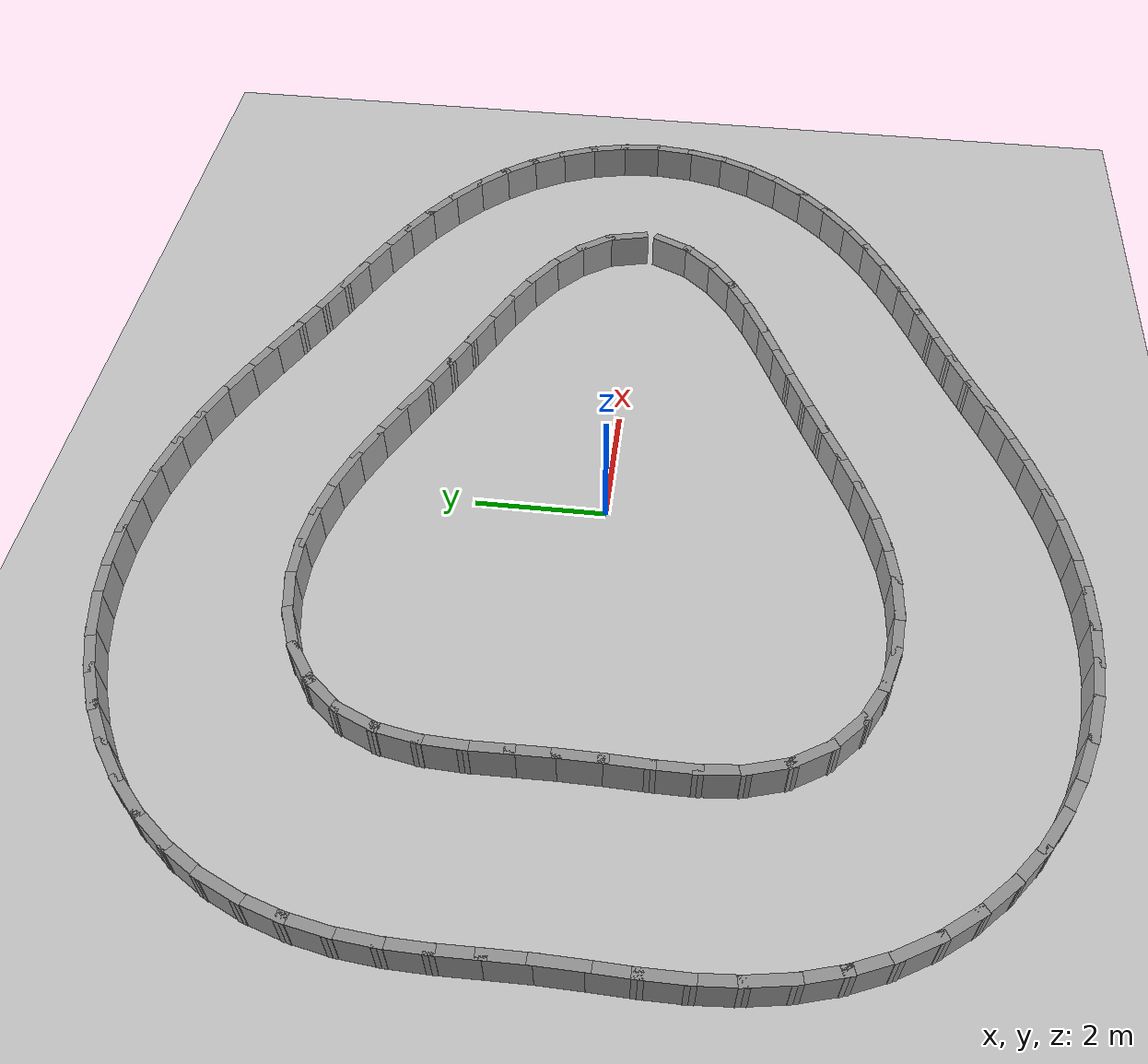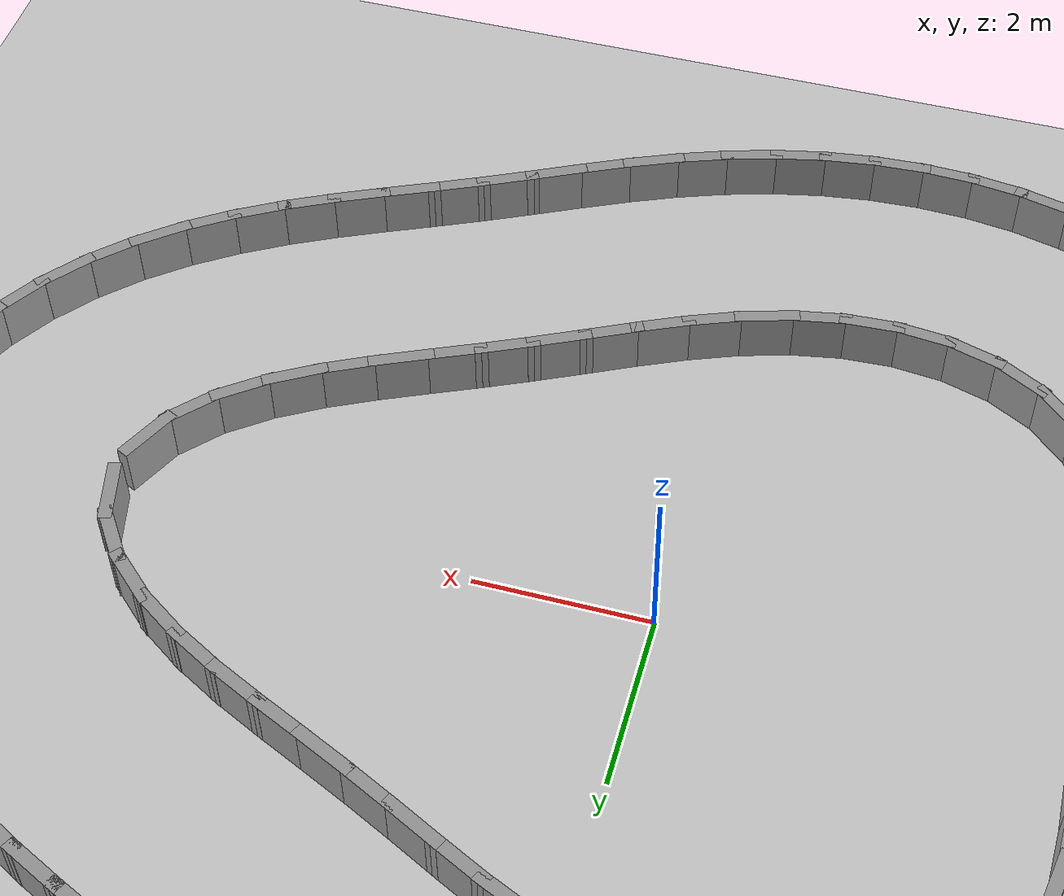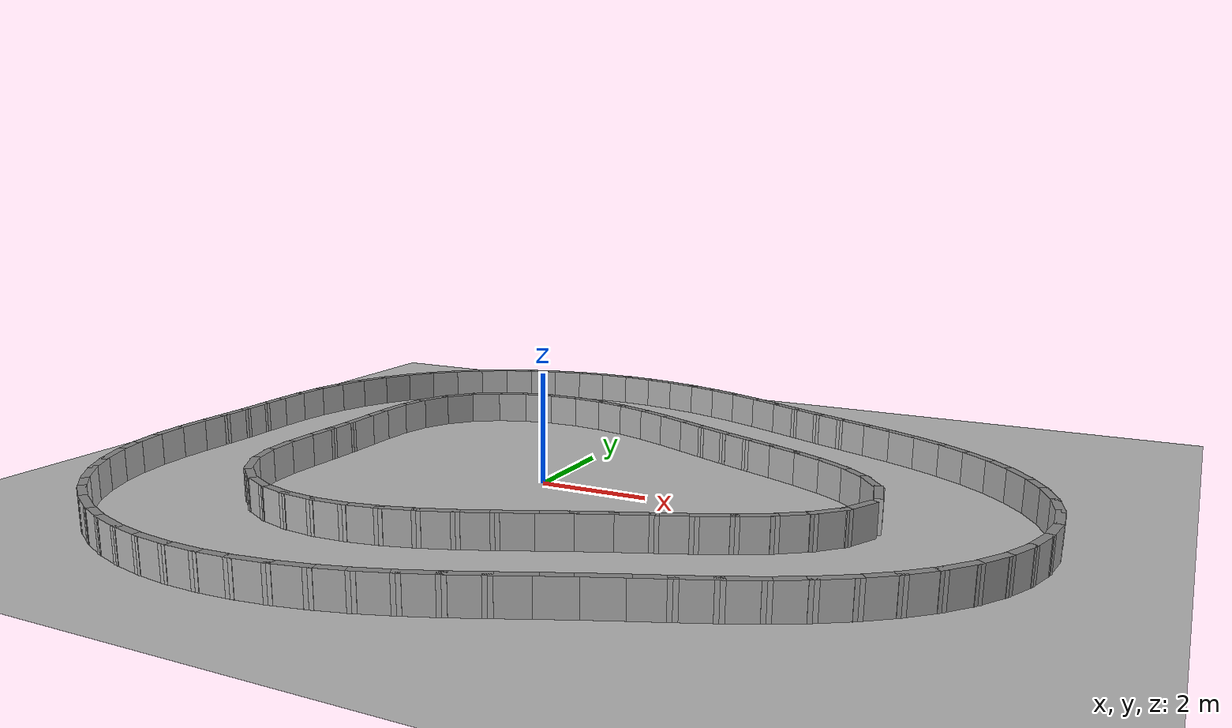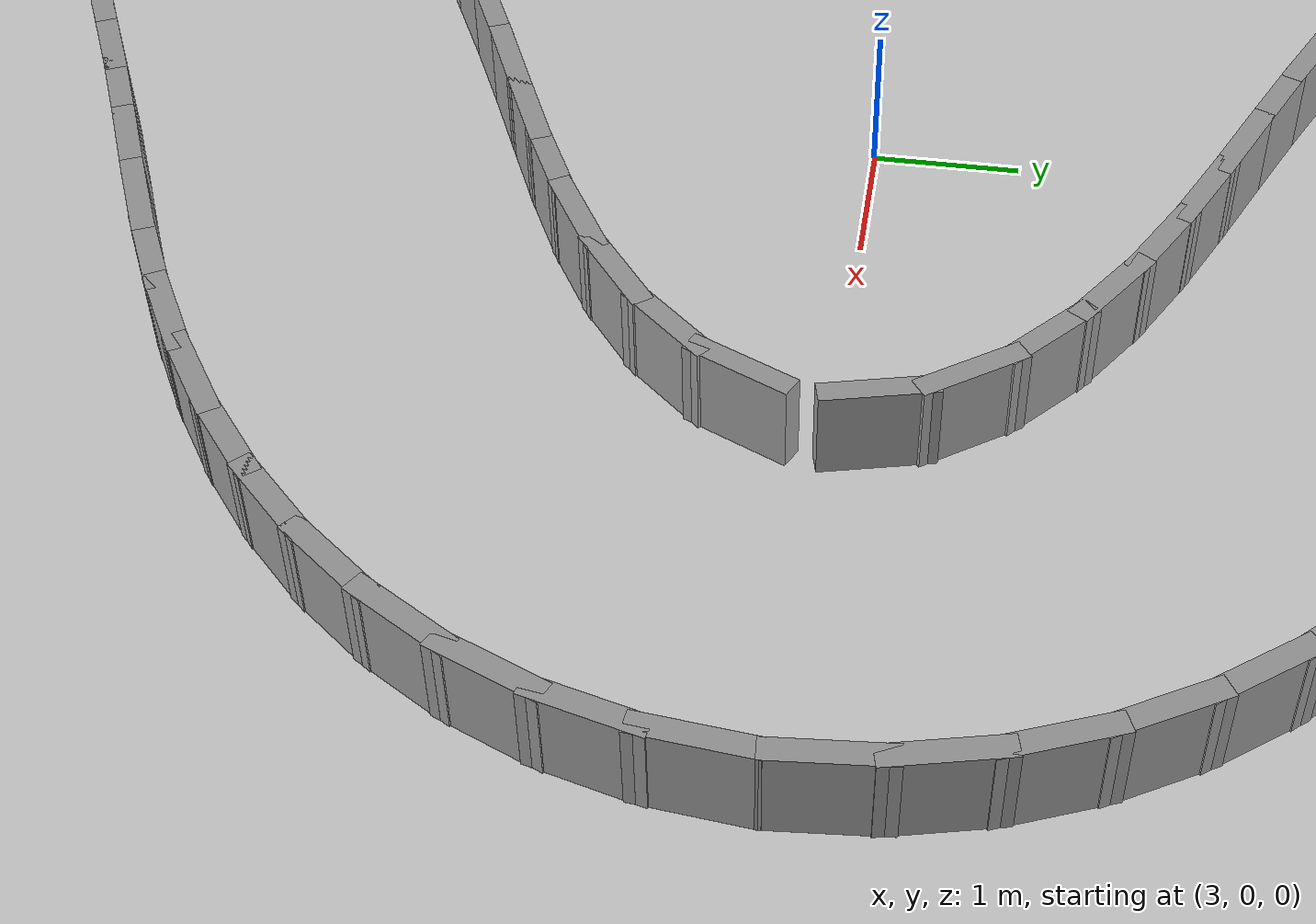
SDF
<?xml version="1.0" ?>
<sdf version='1.7'>
  <world name='default'>
    <plugin name='gazebo_ros_state' filename='libgazebo_ros_state.so'>
      <ros>
        <namespace>/</namespace>
      </ros>
      <update_rate>1000.0</update_rate>
    </plugin>

    <light name='sun' type='directional'>
      <cast_shadows>1</cast_shadows>
      <pose>0 0 10 0 -0 0</pose>
      <diffuse>0.8 0.8 0.8 1</diffuse>
      <specular>0.2 0.2 0.2 1</specular>
      <attenuation>
        <range>1000</range>
        <constant>0.9</constant>
        <linear>0.01</linear>
        <quadratic>0.001</quadratic>
      </attenuation>
      <direction>-0.5 0.1 -0.9</direction>
      <spot>
        <inner_angle>0</inner_angle>
        <outer_angle>0</outer_angle>
        <falloff>0</falloff>
      </spot>
    </light>
    <model name='ground_plane'>
      <static>1</static>
      <link name='link'>
        <collision name='collision'>
          <geometry>
            <plane>
              <normal>0 0 1</normal>
              <size>100 100</size>
            </plane>
          </geometry>
          <surface>
            <friction>
              <ode>
                <mu>100</mu>
                <mu2>50</mu2>
              </ode>
              <torsional>
                <ode/>
              </torsional>
            </friction>
            <contact>
              <ode/>
            </contact>
            <bounce/>
          </surface>
          <max_contacts>10</max_contacts>
        </collision>
        <visual name='visual'>
          <cast_shadows>0</cast_shadows>
          <geometry>
            <plane>
              <normal>0 0 1</normal>
              <size>100 100</size>
            </plane>
          </geometry>
          <material>
            <script>
              <uri>file://media/materials/scripts/gazebo.material</uri>
              <name>Gazebo/Grey</name>
            </script>
          </material>
        </visual>
        <self_collide>0</self_collide>
        <enable_wind>0</enable_wind>
        <kinematic>0</kinematic>
      </link>
    </model>
    <gravity>0 0 -9.8</gravity>
    <magnetic_field>6e-06 2.3e-05 -4.2e-05</magnetic_field>
    <atmosphere type='adiabatic'/>
    <physics type='ode'>
      <max_step_size>0.001</max_step_size>
      <real_time_factor>1</real_time_factor>
      <real_time_update_rate>1000</real_time_update_rate>
    </physics>
    <scene>
      <ambient>0.4 0.4 0.4 1</ambient>
      <background>0.7 0.7 0.7 1</background>
      <shadows>1</shadows>
    </scene>
    <audio>
      <device>default</device>
    </audio>
    <wind/>
    <spherical_coordinates>
      <surface_model>EARTH_WGS84</surface_model>
      <latitude_deg>0</latitude_deg>
      <longitude_deg>0</longitude_deg>
      <elevation>0</elevation>
      <heading_deg>0</heading_deg>
    </spherical_coordinates>
  <model name='rand_lobed_01'>
    <pose>0 0 0 0 -0 0</pose>
    <link name='Wall_0'>
      <collision name='Wall_0_Collision'>
        <geometry><box><size>0.7447 0.1500 0.6000</size></box></geometry>
        <pose>0 0 0.3000 0 -0 0</pose>
      </collision>
      <visual name='Wall_0_Visual'>
        <pose>0 0 0.3000 0 -0 0</pose>
        <geometry><box><size>0.7447 0.1500 0.6000</size></box></geometry>
        <material>
          <script>
            <uri>file://media/materials/scripts/gazebo.material</uri>
            <name>Gazebo/Grey</name>
          </script>
          <ambient>1 1 1 1</ambient>
        </material>
      </visual>
      <pose>5.9368 0.2886 0 0 -0 1.81346</pose>
    </link>
    <link name='Wall_1'>
      <collision name='Wall_1_Collision'>
        <geometry><box><size>0.7480 0.1500 0.6000</size></box></geometry>
        <pose>0 0 0.3000 0 -0 0</pose>
      </collision>
      <visual name='Wall_1_Visual'>
        <pose>0 0 0.3000 0 -0 0</pose>
        <geometry><box><size>0.7480 0.1500 0.6000</size></box></geometry>
        <material>
          <script>
            <uri>file://media/materials/scripts/gazebo.material</uri>
            <name>Gazebo/Grey</name>
          </script>
          <ambient>1 1 1 1</ambient>
        </material>
      </visual>
      <pose>5.6933 0.8218 0 0 -0 2.18384</pose>
    </link>
    <link name='Wall_2'>
      <collision name='Wall_2_Collision'>
        <geometry><box><size>0.7492 0.1500 0.6000</size></box></geometry>
        <pose>0 0 0.3000 0 -0 0</pose>
      </collision>
      <visual name='Wall_2_Visual'>
        <pose>0 0 0.3000 0 -0 0</pose>
        <geometry><box><size>0.7492 0.1500 0.6000</size></box></geometry>
        <material>
          <script>
            <uri>file://media/materials/scripts/gazebo.material</uri>
            <name>Gazebo/Grey</name>
          </script>
          <ambient>1 1 1 1</ambient>
        </material>
      </visual>
      <pose>5.2981 1.2662 0 0 -0 2.41141</pose>
    </link>
    <link name='Wall_3'>
      <collision name='Wall_3_Collision'>
        <geometry><box><size>0.7497 0.1500 0.6000</size></box></geometry>
        <pose>0 0 0.3000 0 -0 0</pose>
      </collision>
      <visual name='Wall_3_Visual'>
        <pose>0 0 0.3000 0 -0 0</pose>
        <geometry><box><size>0.7497 0.1500 0.6000</size></box></geometry>
        <material>
          <script>
            <uri>file://media/materials/scripts/gazebo.material</uri>
            <name>Gazebo/Grey</name>
          </script>
          <ambient>1 1 1 1</ambient>
        </material>
      </visual>
      <pose>4.8248 1.6315 0 0 -0 2.55708</pose>
    </link>
    <link name='Wall_4'>
      <collision name='Wall_4_Collision'>
        <geometry><box><size>0.7499 0.1500 0.6000</size></box></geometry>
        <pose>0 0 0.3000 0 -0 0</pose>
      </collision>
      <visual name='Wall_4_Visual'>
        <pose>0 0 0.3000 0 -0 0</pose>
        <geometry><box><size>0.7499 0.1500 0.6000</size></box></geometry>
        <material>
          <script>
            <uri>file://media/materials/scripts/gazebo.material</uri>
            <name>Gazebo/Grey</name>
          </script>
          <ambient>1 1 1 1</ambient>
        </material>
      </visual>
      <pose>4.3103 1.9384 0 0 -0 2.65016</pose>
    </link>
    <link name='Wall_5'>
      <collision name='Wall_5_Collision'>
        <geometry><box><size>0.7500 0.1500 0.6000</size></box></geometry>
        <pose>0 0 0.3000 0 -0 0</pose>
      </collision>
      <visual name='Wall_5_Visual'>
        <pose>0 0 0.3000 0 -0 0</pose>
        <geometry><box><size>0.7500 0.1500 0.6000</size></box></geometry>
        <material>
          <script>
            <uri>file://media/materials/scripts/gazebo.material</uri>
            <name>Gazebo/Grey</name>
          </script>
          <ambient>1 1 1 1</ambient>
        </material>
      </visual>
      <pose>3.7743 2.2075 0 0 -0 2.70257</pose>
    </link>
    <link name='Wall_6'>
      <collision name='Wall_6_Collision'>
        <geometry><box><size>0.7500 0.1500 0.6000</size></box></geometry>
        <pose>0 0 0.3000 0 -0 0</pose>
      </collision>
      <visual name='Wall_6_Visual'>
        <pose>0 0 0.3000 0 -0 0</pose>
        <geometry><box><size>0.7500 0.1500 0.6000</size></box></geometry>
        <material>
          <script>
            <uri>file://media/materials/scripts/gazebo.material</uri>
            <name>Gazebo/Grey</name>
          </script>
          <ambient>1 1 1 1</ambient>
        </material>
      </visual>
      <pose>3.2290 2.4575 0 0 -0 2.72103</pose>
    </link>
    <link name='Wall_7'>
      <collision name='Wall_7_Collision'>
        <geometry><box><size>0.7500 0.1500 0.6000</size></box></geometry>
        <pose>0 0 0.3000 0 -0 0</pose>
      </collision>
      <visual name='Wall_7_Visual'>
        <pose>0 0 0.3000 0 -0 0</pose>
        <geometry><box><size>0.7500 0.1500 0.6000</size></box></geometry>
        <material>
          <script>
            <uri>file://media/materials/scripts/gazebo.material</uri>
            <name>Gazebo/Grey</name>
          </script>
          <ambient>1 1 1 1</ambient>
        </material>
      </visual>
      <pose>2.6821 2.7043 0 0 -0 2.71419</pose>
    </link>
    <link name='Wall_8'>
      <collision name='Wall_8_Collision'>
        <geometry><box><size>0.7500 0.1500 0.6000</size></box></geometry>
        <pose>0 0 0.3000 0 -0 0</pose>
      </collision>
      <visual name='Wall_8_Visual'>
        <pose>0 0 0.3000 0 -0 0</pose>
        <geometry><box><size>0.7500 0.1500 0.6000</size></box></geometry>
        <material>
          <script>
            <uri>file://media/materials/scripts/gazebo.material</uri>
            <name>Gazebo/Grey</name>
          </script>
          <ambient>1 1 1 1</ambient>
        </material>
      </visual>
      <pose>2.1384 2.9580 0 0 -0 2.69587</pose>
    </link>
    <link name='Wall_9'>
      <collision name='Wall_9_Collision'>
        <geometry><box><size>0.7500 0.1500 0.6000</size></box></geometry>
        <pose>0 0 0.3000 0 -0 0</pose>
      </collision>
      <visual name='Wall_9_Visual'>
        <pose>0 0 0.3000 0 -0 0</pose>
        <geometry><box><size>0.7500 0.1500 0.6000</size></box></geometry>
        <material>
          <script>
            <uri>file://media/materials/scripts/gazebo.material</uri>
            <name>Gazebo/Grey</name>
          </script>
          <ambient>1 1 1 1</ambient>
        </material>
      </visual>
      <pose>1.5986 3.2200 0 0 -0 2.68352</pose>
    </link>
    <link name='Wall_10'>
      <collision name='Wall_10_Collision'>
        <geometry><box><size>0.7500 0.1500 0.6000</size></box></geometry>
        <pose>0 0 0.3000 0 -0 0</pose>
      </collision>
      <visual name='Wall_10_Visual'>
        <pose>0 0 0.3000 0 -0 0</pose>
        <geometry><box><size>0.7500 0.1500 0.6000</size></box></geometry>
        <material>
          <script>
            <uri>file://media/materials/scripts/gazebo.material</uri>
            <name>Gazebo/Grey</name>
          </script>
          <ambient>1 1 1 1</ambient>
        </material>
      </visual>
      <pose>1.0592 3.4827 0 0 -0 2.69310</pose>
    </link>
    <link name='Wall_11'>
      <collision name='Wall_11_Collision'>
        <geometry><box><size>0.7499 0.1500 0.6000</size></box></geometry>
        <pose>0 0 0.3000 0 -0 0</pose>
      </collision>
      <visual name='Wall_11_Visual'>
        <pose>0 0 0.3000 0 -0 0</pose>
        <geometry><box><size>0.7499 0.1500 0.6000</size></box></geometry>
        <material>
          <script>
            <uri>file://media/materials/scripts/gazebo.material</uri>
            <name>Gazebo/Grey</name>
          </script>
          <ambient>1 1 1 1</ambient>
        </material>
      </visual>
      <pose>0.5136 3.7318 0 0 -0 2.73362</pose>
    </link>
    <link name='Wall_12'>
      <collision name='Wall_12_Collision'>
        <geometry><box><size>0.7498 0.1500 0.6000</size></box></geometry>
        <pose>0 0 0.3000 0 -0 0</pose>
      </collision>
      <visual name='Wall_12_Visual'>
        <pose>0 0 0.3000 0 -0 0</pose>
        <geometry><box><size>0.7498 0.1500 0.6000</size></box></geometry>
        <material>
          <script>
            <uri>file://media/materials/scripts/gazebo.material</uri>
            <name>Gazebo/Grey</name>
          </script>
          <ambient>1 1 1 1</ambient>
        </material>
      </visual>
      <pose>-0.0449 3.9497 0 0 -0 2.80566</pose>
    </link>
    <link name='Wall_13'>
      <collision name='Wall_13_Collision'>
        <geometry><box><size>0.7497 0.1500 0.6000</size></box></geometry>
        <pose>0 0 0.3000 0 -0 0</pose>
      </collision>
      <visual name='Wall_13_Visual'>
        <pose>0 0 0.3000 0 -0 0</pose>
        <geometry><box><size>0.7497 0.1500 0.6000</size></box></geometry>
        <material>
          <script>
            <uri>file://media/materials/scripts/gazebo.material</uri>
            <name>Gazebo/Grey</name>
          </script>
          <ambient>1 1 1 1</ambient>
        </material>
      </visual>
      <pose>-0.6195 4.1189 0 0 -0 2.90489</pose>
    </link>
    <link name='Wall_14'>
      <collision name='Wall_14_Collision'>
        <geometry><box><size>0.7496 0.1500 0.6000</size></box></geometry>
        <pose>0 0 0.3000 0 -0 0</pose>
      </collision>
      <visual name='Wall_14_Visual'>
        <pose>0 0 0.3000 0 -0 0</pose>
        <geometry><box><size>0.7496 0.1500 0.6000</size></box></geometry>
        <material>
          <script>
            <uri>file://media/materials/scripts/gazebo.material</uri>
            <name>Gazebo/Grey</name>
          </script>
          <ambient>1 1 1 1</ambient>
        </material>
      </visual>
      <pose>-1.2088 4.2235 0 0 -0 3.02691</pose>
    </link>
    <link name='Wall_15'>
      <collision name='Wall_15_Collision'>
        <geometry><box><size>0.7494 0.1500 0.6000</size></box></geometry>
        <pose>0 0 0.3000 0 -0 0</pose>
      </collision>
      <visual name='Wall_15_Visual'>
        <pose>0 0 0.3000 0 -0 0</pose>
        <geometry><box><size>0.7494 0.1500 0.6000</size></box></geometry>
        <material>
          <script>
            <uri>file://media/materials/scripts/gazebo.material</uri>
            <name>Gazebo/Grey</name>
          </script>
          <ambient>1 1 1 1</ambient>
        </material>
      </visual>
      <pose>-1.8062 4.2493 0 0 -0 -3.11310</pose>
    </link>
    <link name='Wall_16'>
      <collision name='Wall_16_Collision'>
        <geometry><box><size>0.7492 0.1500 0.6000</size></box></geometry>
        <pose>0 0 0.3000 0 -0 0</pose>
      </collision>
      <visual name='Wall_16_Visual'>
        <pose>0 0 0.3000 0 -0 0</pose>
        <geometry><box><size>0.7492 0.1500 0.6000</size></box></geometry>
        <material>
          <script>
            <uri>file://media/materials/scripts/gazebo.material</uri>
            <name>Gazebo/Grey</name>
          </script>
          <ambient>1 1 1 1</ambient>
        </material>
      </visual>
      <pose>-2.3997 4.1826 0 0 -0 -2.94653</pose>
    </link>
    <link name='Wall_17'>
      <collision name='Wall_17_Collision'>
        <geometry><box><size>0.7489 0.1500 0.6000</size></box></geometry>
        <pose>0 0 0.3000 0 -0 0</pose>
      </collision>
      <visual name='Wall_17_Visual'>
        <pose>0 0 0.3000 0 -0 0</pose>
        <geometry><box><size>0.7489 0.1500 0.6000</size></box></geometry>
        <material>
          <script>
            <uri>file://media/materials/scripts/gazebo.material</uri>
            <name>Gazebo/Grey</name>
          </script>
          <ambient>1 1 1 1</ambient>
        </material>
      </visual>
      <pose>-2.9705 4.0105 0 0 -0 -2.75075</pose>
    </link>
    <link name='Wall_18'>
      <collision name='Wall_18_Collision'>
        <geometry><box><size>0.7484 0.1500 0.6000</size></box></geometry>
        <pose>0 0 0.3000 0 -0 0</pose>
      </collision>
      <visual name='Wall_18_Visual'>
        <pose>0 0 0.3000 0 -0 0</pose>
        <geometry><box><size>0.7484 0.1500 0.6000</size></box></geometry>
        <material>
          <script>
            <uri>file://media/materials/scripts/gazebo.material</uri>
            <name>Gazebo/Grey</name>
          </script>
          <ambient>1 1 1 1</ambient>
        </material>
      </visual>
      <pose>-3.4902 3.7217 0 0 -0 -2.51799</pose>
    </link>
    <link name='Wall_19'>
      <collision name='Wall_19_Collision'>
        <geometry><box><size>0.7480 0.1500 0.6000</size></box></geometry>
        <pose>0 0 0.3000 0 -0 0</pose>
      </collision>
      <visual name='Wall_19_Visual'>
        <pose>0 0 0.3000 0 -0 0</pose>
        <geometry><box><size>0.7480 0.1500 0.6000</size></box></geometry>
        <material>
          <script>
            <uri>file://media/materials/scripts/gazebo.material</uri>
            <name>Gazebo/Grey</name>
          </script>
          <ambient>1 1 1 1</ambient>
        </material>
      </visual>
      <pose>-3.9207 3.3141 0 0 -0 -2.24880</pose>
    </link>
    <link name='Wall_20'>
      <collision name='Wall_20_Collision'>
        <geometry><box><size>0.7483 0.1500 0.6000</size></box></geometry>
        <pose>0 0 0.3000 0 -0 0</pose>
      </collision>
      <visual name='Wall_20_Visual'>
        <pose>0 0 0.3000 0 -0 0</pose>
        <geometry><box><size>0.7483 0.1500 0.6000</size></box></geometry>
        <material>
          <script>
            <uri>file://media/materials/scripts/gazebo.material</uri>
            <name>Gazebo/Grey</name>
          </script>
          <ambient>1 1 1 1</ambient>
        </material>
      </visual>
      <pose>-4.2255 2.8060 0 0 -0 -1.97364</pose>
    </link>
    <link name='Wall_21'>
      <collision name='Wall_21_Collision'>
        <geometry><box><size>0.7491 0.1500 0.6000</size></box></geometry>
        <pose>0 0 0.3000 0 -0 0</pose>
      </collision>
      <visual name='Wall_21_Visual'>
        <pose>0 0 0.3000 0 -0 0</pose>
        <geometry><box><size>0.7491 0.1500 0.6000</size></box></geometry>
        <material>
          <script>
            <uri>file://media/materials/scripts/gazebo.material</uri>
            <name>Gazebo/Grey</name>
          </script>
          <ambient>1 1 1 1</ambient>
        </material>
      </visual>
      <pose>-4.3958 2.2360 0 0 -0 -1.74892</pose>
    </link>
    <link name='Wall_22'>
      <collision name='Wall_22_Collision'>
        <geometry><box><size>0.7498 0.1500 0.6000</size></box></geometry>
        <pose>0 0 0.3000 0 -0 0</pose>
      </collision>
      <visual name='Wall_22_Visual'>
        <pose>0 0 0.3000 0 -0 0</pose>
        <geometry><box><size>0.7498 0.1500 0.6000</size></box></geometry>
        <material>
          <script>
            <uri>file://media/materials/scripts/gazebo.material</uri>
            <name>Gazebo/Grey</name>
          </script>
          <ambient>1 1 1 1</ambient>
        </material>
      </visual>
      <pose>-4.4603 1.6415 0 0 -0 -1.60867</pose>
    </link>
    <link name='Wall_23'>
      <collision name='Wall_23_Collision'>
        <geometry><box><size>0.7500 0.1500 0.6000</size></box></geometry>
        <pose>0 0 0.3000 0 -0 0</pose>
      </collision>
      <visual name='Wall_23_Visual'>
        <pose>0 0 0.3000 0 -0 0</pose>
        <geometry><box><size>0.7500 0.1500 0.6000</size></box></geometry>
        <material>
          <script>
            <uri>file://media/materials/scripts/gazebo.material</uri>
            <name>Gazebo/Grey</name>
          </script>
          <ambient>1 1 1 1</ambient>
        </material>
      </visual>
      <pose>-4.4655 1.0419 0 0 -0 -1.55020</pose>
    </link>
    <link name='Wall_24'>
      <collision name='Wall_24_Collision'>
        <geometry><box><size>0.7500 0.1500 0.6000</size></box></geometry>
        <pose>0 0 0.3000 0 -0 0</pose>
      </collision>
      <visual name='Wall_24_Visual'>
        <pose>0 0 0.3000 0 -0 0</pose>
        <geometry><box><size>0.7500 0.1500 0.6000</size></box></geometry>
        <material>
          <script>
            <uri>file://media/materials/scripts/gazebo.material</uri>
            <name>Gazebo/Grey</name>
          </script>
          <ambient>1 1 1 1</ambient>
        </material>
      </visual>
      <pose>-4.4533 0.4420 0 0 -0 -1.55099</pose>
    </link>
    <link name='Wall_25'>
      <collision name='Wall_25_Collision'>
        <geometry><box><size>0.7500 0.1500 0.6000</size></box></geometry>
        <pose>0 0 0.3000 0 -0 0</pose>
      </collision>
      <visual name='Wall_25_Visual'>
        <pose>0 0 0.3000 0 -0 0</pose>
        <geometry><box><size>0.7500 0.1500 0.6000</size></box></geometry>
        <material>
          <script>
            <uri>file://media/materials/scripts/gazebo.material</uri>
            <name>Gazebo/Grey</name>
          </script>
          <ambient>1 1 1 1</ambient>
        </material>
      </visual>
      <pose>-4.4497 -0.1579 0 0 -0 -1.57864</pose>
    </link>
    <link name='Wall_26'>
      <collision name='Wall_26_Collision'>
        <geometry><box><size>0.7500 0.1500 0.6000</size></box></geometry>
        <pose>0 0 0.3000 0 -0 0</pose>
      </collision>
      <visual name='Wall_26_Visual'>
        <pose>0 0 0.3000 0 -0 0</pose>
        <geometry><box><size>0.7500 0.1500 0.6000</size></box></geometry>
        <material>
          <script>
            <uri>file://media/materials/scripts/gazebo.material</uri>
            <name>Gazebo/Grey</name>
          </script>
          <ambient>1 1 1 1</ambient>
        </material>
      </visual>
      <pose>-4.4598 -0.7578 0 0 -0 -1.59659</pose>
    </link>
    <link name='Wall_27'>
      <collision name='Wall_27_Collision'>
        <geometry><box><size>0.7499 0.1500 0.6000</size></box></geometry>
        <pose>0 0 0.3000 0 -0 0</pose>
      </collision>
      <visual name='Wall_27_Visual'>
        <pose>0 0 0.3000 0 -0 0</pose>
        <geometry><box><size>0.7499 0.1500 0.6000</size></box></geometry>
        <material>
          <script>
            <uri>file://media/materials/scripts/gazebo.material</uri>
            <name>Gazebo/Grey</name>
          </script>
          <ambient>1 1 1 1</ambient>
        </material>
      </visual>
      <pose>-4.4673 -1.3576 0 0 -0 -1.56974</pose>
    </link>
    <link name='Wall_28'>
      <collision name='Wall_28_Collision'>
        <geometry><box><size>0.7495 0.1500 0.6000</size></box></geometry>
        <pose>0 0 0.3000 0 -0 0</pose>
      </collision>
      <visual name='Wall_28_Visual'>
        <pose>0 0 0.3000 0 -0 0</pose>
        <geometry><box><size>0.7495 0.1500 0.6000</size></box></geometry>
        <material>
          <script>
            <uri>file://media/materials/scripts/gazebo.material</uri>
            <name>Gazebo/Grey</name>
          </script>
          <ambient>1 1 1 1</ambient>
        </material>
      </visual>
      <pose>-4.4368 -1.9558 0 0 -0 -1.47012</pose>
    </link>
    <link name='Wall_29'>
      <collision name='Wall_29_Collision'>
        <geometry><box><size>0.7487 0.1500 0.6000</size></box></geometry>
        <pose>0 0 0.3000 0 -0 0</pose>
      </collision>
      <visual name='Wall_29_Visual'>
        <pose>0 0 0.3000 0 -0 0</pose>
        <geometry><box><size>0.7487 0.1500 0.6000</size></box></geometry>
        <material>
          <script>
            <uri>file://media/materials/scripts/gazebo.material</uri>
            <name>Gazebo/Grey</name>
          </script>
          <ambient>1 1 1 1</ambient>
        </material>
      </visual>
      <pose>-4.3219 -2.5411 0 0 -0 -1.28377</pose>
    </link>
    <link name='Wall_30'>
      <collision name='Wall_30_Collision'>
        <geometry><box><size>0.7480 0.1500 0.6000</size></box></geometry>
        <pose>0 0 0.3000 0 -0 0</pose>
      </collision>
      <visual name='Wall_30_Visual'>
        <pose>0 0 0.3000 0 -0 0</pose>
        <geometry><box><size>0.7480 0.1500 0.6000</size></box></geometry>
        <material>
          <script>
            <uri>file://media/materials/scripts/gazebo.material</uri>
            <name>Gazebo/Grey</name>
          </script>
          <ambient>1 1 1 1</ambient>
        </material>
      </visual>
      <pose>-4.0822 -3.0839 0 0 -0 -1.02574</pose>
    </link>
    <link name='Wall_31'>
      <collision name='Wall_31_Collision'>
        <geometry><box><size>0.7482 0.1500 0.6000</size></box></geometry>
        <pose>0 0 0.3000 0 -0 0</pose>
      </collision>
      <visual name='Wall_31_Visual'>
        <pose>0 0 0.3000 0 -0 0</pose>
        <geometry><box><size>0.7482 0.1500 0.6000</size></box></geometry>
        <material>
          <script>
            <uri>file://media/materials/scripts/gazebo.material</uri>
            <name>Gazebo/Grey</name>
          </script>
          <ambient>1 1 1 1</ambient>
        </material>
      </visual>
      <pose>-3.7078 -3.5429 0 0 -0 -0.74746</pose>
    </link>
    <link name='Wall_32'>
      <collision name='Wall_32_Collision'>
        <geometry><box><size>0.7487 0.1500 0.6000</size></box></geometry>
        <pose>0 0 0.3000 0 -0 0</pose>
      </collision>
      <visual name='Wall_32_Visual'>
        <pose>0 0 0.3000 0 -0 0</pose>
        <geometry><box><size>0.7487 0.1500 0.6000</size></box></geometry>
        <material>
          <script>
            <uri>file://media/materials/scripts/gazebo.material</uri>
            <name>Gazebo/Grey</name>
          </script>
          <ambient>1 1 1 1</ambient>
        </material>
      </visual>
      <pose>-3.2252 -3.8887 0 0 -0 -0.49611</pose>
    </link>
    <link name='Wall_33'>
      <collision name='Wall_33_Collision'>
        <geometry><box><size>0.7491 0.1500 0.6000</size></box></geometry>
        <pose>0 0 0.3000 0 -0 0</pose>
      </collision>
      <visual name='Wall_33_Visual'>
        <pose>0 0 0.3000 0 -0 0</pose>
        <geometry><box><size>0.7491 0.1500 0.6000</size></box></geometry>
        <material>
          <script>
            <uri>file://media/materials/scripts/gazebo.material</uri>
            <name>Gazebo/Grey</name>
          </script>
          <ambient>1 1 1 1</ambient>
        </material>
      </visual>
      <pose>-2.6744 -4.1150 0 0 -0 -0.28367</pose>
    </link>
    <link name='Wall_34'>
      <collision name='Wall_34_Collision'>
        <geometry><box><size>0.7493 0.1500 0.6000</size></box></geometry>
        <pose>0 0 0.3000 0 -0 0</pose>
      </collision>
      <visual name='Wall_34_Visual'>
        <pose>0 0 0.3000 0 -0 0</pose>
        <geometry><box><size>0.7493 0.1500 0.6000</size></box></geometry>
        <material>
          <script>
            <uri>file://media/materials/scripts/gazebo.material</uri>
            <name>Gazebo/Grey</name>
          </script>
          <ambient>1 1 1 1</ambient>
        </material>
      </visual>
      <pose>-2.0888 -4.2300 0 0 -0 -0.10419</pose>
    </link>
    <link name='Wall_35'>
      <collision name='Wall_35_Collision'>
        <geometry><box><size>0.7495 0.1500 0.6000</size></box></geometry>
        <pose>0 0 0.3000 0 -0 0</pose>
      </collision>
      <visual name='Wall_35_Visual'>
        <pose>0 0 0.3000 0 -0 0</pose>
        <geometry><box><size>0.7495 0.1500 0.6000</size></box></geometry>
        <material>
          <script>
            <uri>file://media/materials/scripts/gazebo.material</uri>
            <name>Gazebo/Grey</name>
          </script>
          <ambient>1 1 1 1</ambient>
        </material>
      </visual>
      <pose>-1.4914 -4.2464 0 0 -0 0.04955</pose>
    </link>
    <link name='Wall_36'>
      <collision name='Wall_36_Collision'>
        <geometry><box><size>0.7496 0.1500 0.6000</size></box></geometry>
        <pose>0 0 0.3000 0 -0 0</pose>
      </collision>
      <visual name='Wall_36_Visual'>
        <pose>0 0 0.3000 0 -0 0</pose>
        <geometry><box><size>0.7496 0.1500 0.6000</size></box></geometry>
        <material>
          <script>
            <uri>file://media/materials/scripts/gazebo.material</uri>
            <name>Gazebo/Grey</name>
          </script>
          <ambient>1 1 1 1</ambient>
        </material>
      </visual>
      <pose>-0.8971 -4.1774 0 0 -0 0.18156</pose>
    </link>
    <link name='Wall_37'>
      <collision name='Wall_37_Collision'>
        <geometry><box><size>0.7498 0.1500 0.6000</size></box></geometry>
        <pose>0 0 0.3000 0 -0 0</pose>
      </collision>
      <visual name='Wall_37_Visual'>
        <pose>0 0 0.3000 0 -0 0</pose>
        <geometry><box><size>0.7498 0.1500 0.6000</size></box></geometry>
        <material>
          <script>
            <uri>file://media/materials/scripts/gazebo.material</uri>
            <name>Gazebo/Grey</name>
          </script>
          <ambient>1 1 1 1</ambient>
        </material>
      </visual>
      <pose>-0.3150 -4.0369 0 0 -0 0.29200</pose>
    </link>
    <link name='Wall_38'>
      <collision name='Wall_38_Collision'>
        <geometry><box><size>0.7499 0.1500 0.6000</size></box></geometry>
        <pose>0 0 0.3000 0 -0 0</pose>
      </collision>
      <visual name='Wall_38_Visual'>
        <pose>0 0 0.3000 0 -0 0</pose>
        <geometry><box><size>0.7499 0.1500 0.6000</size></box></geometry>
        <material>
          <script>
            <uri>file://media/materials/scripts/gazebo.material</uri>
            <name>Gazebo/Grey</name>
          </script>
          <ambient>1 1 1 1</ambient>
        </material>
      </visual>
      <pose>0.2510 -3.8400 0 0 -0 0.37757</pose>
    </link>
    <link name='Wall_39'>
      <collision name='Wall_39_Collision'>
        <geometry><box><size>0.7500 0.1500 0.6000</size></box></geometry>
        <pose>0 0 0.3000 0 -0 0</pose>
      </collision>
      <visual name='Wall_39_Visual'>
        <pose>0 0 0.3000 0 -0 0</pose>
        <geometry><box><size>0.7500 0.1500 0.6000</size></box></geometry>
        <material>
          <script>
            <uri>file://media/materials/scripts/gazebo.material</uri>
            <name>Gazebo/Grey</name>
          </script>
          <ambient>1 1 1 1</ambient>
        </material>
      </visual>
      <pose>0.8020 -3.6035 0 0 -0 0.43337</pose>
    </link>
    <link name='Wall_40'>
      <collision name='Wall_40_Collision'>
        <geometry><box><size>0.7500 0.1500 0.6000</size></box></geometry>
        <pose>0 0 0.3000 0 -0 0</pose>
      </collision>
      <visual name='Wall_40_Visual'>
        <pose>0 0 0.3000 0 -0 0</pose>
        <geometry><box><size>0.7500 0.1500 0.6000</size></box></geometry>
        <material>
          <script>
            <uri>file://media/materials/scripts/gazebo.material</uri>
            <name>Gazebo/Grey</name>
          </script>
          <ambient>1 1 1 1</ambient>
        </material>
      </visual>
      <pose>1.3435 -3.3451 0 0 -0 0.45703</pose>
    </link>
    <link name='Wall_41'>
      <collision name='Wall_41_Collision'>
        <geometry><box><size>0.7500 0.1500 0.6000</size></box></geometry>
        <pose>0 0 0.3000 0 -0 0</pose>
      </collision>
      <visual name='Wall_41_Visual'>
        <pose>0 0 0.3000 0 -0 0</pose>
        <geometry><box><size>0.7500 0.1500 0.6000</size></box></geometry>
        <material>
          <script>
            <uri>file://media/materials/scripts/gazebo.material</uri>
            <name>Gazebo/Grey</name>
          </script>
          <ambient>1 1 1 1</ambient>
        </material>
      </visual>
      <pose>1.8824 -3.0813 0 0 -0 0.45340</pose>
    </link>
    <link name='Wall_42'>
      <collision name='Wall_42_Collision'>
        <geometry><box><size>0.7500 0.1500 0.6000</size></box></geometry>
        <pose>0 0 0.3000 0 -0 0</pose>
      </collision>
      <visual name='Wall_42_Visual'>
        <pose>0 0 0.3000 0 -0 0</pose>
        <geometry><box><size>0.7500 0.1500 0.6000</size></box></geometry>
        <material>
          <script>
            <uri>file://media/materials/scripts/gazebo.material</uri>
            <name>Gazebo/Grey</name>
          </script>
          <ambient>1 1 1 1</ambient>
        </material>
      </visual>
      <pose>2.4240 -2.8233 0 0 -0 0.43568</pose>
    </link>
    <link name='Wall_43'>
      <collision name='Wall_43_Collision'>
        <geometry><box><size>0.7500 0.1500 0.6000</size></box></geometry>
        <pose>0 0 0.3000 0 -0 0</pose>
      </collision>
      <visual name='Wall_43_Visual'>
        <pose>0 0 0.3000 0 -0 0</pose>
        <geometry><box><size>0.7500 0.1500 0.6000</size></box></geometry>
        <material>
          <script>
            <uri>file://media/materials/scripts/gazebo.material</uri>
            <name>Gazebo/Grey</name>
          </script>
          <ambient>1 1 1 1</ambient>
        </material>
      </visual>
      <pose>2.9697 -2.5740 0 0 -0 0.42137</pose>
    </link>
    <link name='Wall_44'>
      <collision name='Wall_44_Collision'>
        <geometry><box><size>0.7500 0.1500 0.6000</size></box></geometry>
        <pose>0 0 0.3000 0 -0 0</pose>
      </collision>
      <visual name='Wall_44_Visual'>
        <pose>0 0 0.3000 0 -0 0</pose>
        <geometry><box><size>0.7500 0.1500 0.6000</size></box></geometry>
        <material>
          <script>
            <uri>file://media/materials/scripts/gazebo.material</uri>
            <name>Gazebo/Grey</name>
          </script>
          <ambient>1 1 1 1</ambient>
        </material>
      </visual>
      <pose>3.5166 -2.3272 0 0 -0 0.42648</pose>
    </link>
    <link name='Wall_45'>
      <collision name='Wall_45_Collision'>
        <geometry><box><size>0.7499 0.1500 0.6000</size></box></geometry>
        <pose>0 0 0.3000 0 -0 0</pose>
      </collision>
      <visual name='Wall_45_Visual'>
        <pose>0 0 0.3000 0 -0 0</pose>
        <geometry><box><size>0.7499 0.1500 0.6000</size></box></geometry>
        <material>
          <script>
            <uri>file://media/materials/scripts/gazebo.material</uri>
            <name>Gazebo/Grey</name>
          </script>
          <ambient>1 1 1 1</ambient>
        </material>
      </visual>
      <pose>4.0583 -2.0694 0 0 -0 0.46196</pose>
    </link>
    <link name='Wall_46'>
      <collision name='Wall_46_Collision'>
        <geometry><box><size>0.7498 0.1500 0.6000</size></box></geometry>
        <pose>0 0 0.3000 0 -0 0</pose>
      </collision>
      <visual name='Wall_46_Visual'>
        <pose>0 0 0.3000 0 -0 0</pose>
        <geometry><box><size>0.7498 0.1500 0.6000</size></box></geometry>
        <material>
          <script>
            <uri>file://media/materials/scripts/gazebo.material</uri>
            <name>Gazebo/Grey</name>
          </script>
          <ambient>1 1 1 1</ambient>
        </material>
      </visual>
      <pose>4.5848 -1.7828 0 0 -0 0.53483</pose>
    </link>
    <link name='Wall_47'>
      <collision name='Wall_47_Collision'>
        <geometry><box><size>0.7495 0.1500 0.6000</size></box></geometry>
        <pose>0 0 0.3000 0 -0 0</pose>
      </collision>
      <visual name='Wall_47_Visual'>
        <pose>0 0 0.3000 0 -0 0</pose>
        <geometry><box><size>0.7495 0.1500 0.6000</size></box></geometry>
        <material>
          <script>
            <uri>file://media/materials/scripts/gazebo.material</uri>
            <name>Gazebo/Grey</name>
          </script>
          <ambient>1 1 1 1</ambient>
        </material>
      </visual>
      <pose>5.0808 -1.4478 0 0 -0 0.65340</pose>
    </link>
    <link name='Wall_48'>
      <collision name='Wall_48_Collision'>
        <geometry><box><size>0.7487 0.1500 0.6000</size></box></geometry>
        <pose>0 0 0.3000 0 -0 0</pose>
      </collision>
      <visual name='Wall_48_Visual'>
        <pose>0 0 0.3000 0 -0 0</pose>
        <geometry><box><size>0.7487 0.1500 0.6000</size></box></geometry>
        <material>
          <script>
            <uri>file://media/materials/scripts/gazebo.material</uri>
            <name>Gazebo/Grey</name>
          </script>
          <ambient>1 1 1 1</ambient>
        </material>
      </visual>
      <pose>5.5194 -1.0434 0 0 -0 0.83661</pose>
    </link>
    <link name='Wall_49'>
      <collision name='Wall_49_Collision'>
        <geometry><box><size>0.7465 0.1500 0.6000</size></box></geometry>
        <pose>0 0 0.3000 0 -0 0</pose>
      </collision>
      <visual name='Wall_49_Visual'>
        <pose>0 0 0.3000 0 -0 0</pose>
        <geometry><box><size>0.7465 0.1500 0.6000</size></box></geometry>
        <material>
          <script>
            <uri>file://media/materials/scripts/gazebo.material</uri>
            <name>Gazebo/Grey</name>
          </script>
          <ambient>1 1 1 1</ambient>
        </material>
      </visual>
      <pose>5.8470 -0.5513 0 0 -0 1.13068</pose>
    </link>
    <link name='Wall_50'>
      <collision name='Wall_50_Collision'>
        <geometry><box><size>0.7494 0.1500 0.6000</size></box></geometry>
        <pose>0 0 0.3000 0 -0 0</pose>
      </collision>
      <visual name='Wall_50_Visual'>
        <pose>0 0 0.3000 0 -0 0</pose>
        <geometry><box><size>0.7494 0.1500 0.6000</size></box></geometry>
        <material>
          <script>
            <uri>file://media/materials/scripts/gazebo.material</uri>
            <name>Gazebo/Grey</name>
          </script>
          <ambient>1 1 1 1</ambient>
        </material>
      </visual>
      <pose>8.6292 0.2988 0 0 -0 1.64962</pose>
    </link>
    <link name='Wall_51'>
      <collision name='Wall_51_Collision'>
        <geometry><box><size>0.7494 0.1500 0.6000</size></box></geometry>
        <pose>0 0 0.3000 0 -0 0</pose>
      </collision>
      <visual name='Wall_51_Visual'>
        <pose>0 0 0.3000 0 -0 0</pose>
        <geometry><box><size>0.7494 0.1500 0.6000</size></box></geometry>
        <material>
          <script>
            <uri>file://media/materials/scripts/gazebo.material</uri>
            <name>Gazebo/Grey</name>
          </script>
          <ambient>1 1 1 1</ambient>
        </material>
      </visual>
      <pose>8.5361 0.8890 0 0 -0 1.80491</pose>
    </link>
    <link name='Wall_52'>
      <collision name='Wall_52_Collision'>
        <geometry><box><size>0.7495 0.1500 0.6000</size></box></geometry>
        <pose>0 0 0.3000 0 -0 0</pose>
      </collision>
      <visual name='Wall_52_Visual'>
        <pose>0 0 0.3000 0 -0 0</pose>
        <geometry><box><size>0.7495 0.1500 0.6000</size></box></geometry>
        <material>
          <script>
            <uri>file://media/materials/scripts/gazebo.material</uri>
            <name>Gazebo/Grey</name>
          </script>
          <ambient>1 1 1 1</ambient>
        </material>
      </visual>
      <pose>8.3545 1.4585 0 0 -0 1.95424</pose>
    </link>
    <link name='Wall_53'>
      <collision name='Wall_53_Collision'>
        <geometry><box><size>0.7495 0.1500 0.6000</size></box></geometry>
        <pose>0 0 0.3000 0 -0 0</pose>
      </collision>
      <visual name='Wall_53_Visual'>
        <pose>0 0 0.3000 0 -0 0</pose>
        <geometry><box><size>0.7495 0.1500 0.6000</size></box></geometry>
        <material>
          <script>
            <uri>file://media/materials/scripts/gazebo.material</uri>
            <name>Gazebo/Grey</name>
          </script>
          <ambient>1 1 1 1</ambient>
        </material>
      </visual>
      <pose>8.0924 1.9961 0 0 -0 2.09437</pose>
    </link>
    <link name='Wall_54'>
      <collision name='Wall_54_Collision'>
        <geometry><box><size>0.7496 0.1500 0.6000</size></box></geometry>
        <pose>0 0 0.3000 0 -0 0</pose>
      </collision>
      <visual name='Wall_54_Visual'>
        <pose>0 0 0.3000 0 -0 0</pose>
        <geometry><box><size>0.7496 0.1500 0.6000</size></box></geometry>
        <material>
          <script>
            <uri>file://media/materials/scripts/gazebo.material</uri>
            <name>Gazebo/Grey</name>
          </script>
          <ambient>1 1 1 1</ambient>
        </material>
      </visual>
      <pose>7.7606 2.4940 0 0 -0 2.22297</pose>
    </link>
    <link name='Wall_55'>
      <collision name='Wall_55_Collision'>
        <geometry><box><size>0.7497 0.1500 0.6000</size></box></geometry>
        <pose>0 0 0.3000 0 -0 0</pose>
      </collision>
      <visual name='Wall_55_Visual'>
        <pose>0 0 0.3000 0 -0 0</pose>
        <geometry><box><size>0.7497 0.1500 0.6000</size></box></geometry>
        <material>
          <script>
            <uri>file://media/materials/scripts/gazebo.material</uri>
            <name>Gazebo/Grey</name>
          </script>
          <ambient>1 1 1 1</ambient>
        </material>
      </visual>
      <pose>7.3703 2.9480 0 0 -0 2.33893</pose>
    </link>
    <link name='Wall_56'>
      <collision name='Wall_56_Collision'>
        <geometry><box><size>0.7498 0.1500 0.6000</size></box></geometry>
        <pose>0 0 0.3000 0 -0 0</pose>
      </collision>
      <visual name='Wall_56_Visual'>
        <pose>0 0 0.3000 0 -0 0</pose>
        <geometry><box><size>0.7498 0.1500 0.6000</size></box></geometry>
        <material>
          <script>
            <uri>file://media/materials/scripts/gazebo.material</uri>
            <name>Gazebo/Grey</name>
          </script>
          <ambient>1 1 1 1</ambient>
        </material>
      </visual>
      <pose>6.9326 3.3568 0 0 -0 2.44145</pose>
    </link>
    <link name='Wall_57'>
      <collision name='Wall_57_Collision'>
        <geometry><box><size>0.7498 0.1500 0.6000</size></box></geometry>
        <pose>0 0 0.3000 0 -0 0</pose>
      </collision>
      <visual name='Wall_57_Visual'>
        <pose>0 0 0.3000 0 -0 0</pose>
        <geometry><box><size>0.7498 0.1500 0.6000</size></box></geometry>
        <material>
          <script>
            <uri>file://media/materials/scripts/gazebo.material</uri>
            <name>Gazebo/Grey</name>
          </script>
          <ambient>1 1 1 1</ambient>
        </material>
      </visual>
      <pose>6.4577 3.7222 0 0 -0 2.53033</pose>
    </link>
    <link name='Wall_58'>
      <collision name='Wall_58_Collision'>
        <geometry><box><size>0.7499 0.1500 0.6000</size></box></geometry>
        <pose>0 0 0.3000 0 -0 0</pose>
      </collision>
      <visual name='Wall_58_Visual'>
        <pose>0 0 0.3000 0 -0 0</pose>
        <geometry><box><size>0.7499 0.1500 0.6000</size></box></geometry>
        <material>
          <script>
            <uri>file://media/materials/scripts/gazebo.material</uri>
            <name>Gazebo/Grey</name>
          </script>
          <ambient>1 1 1 1</ambient>
        </material>
      </visual>
      <pose>5.9543 4.0477 0 0 -0 2.60478</pose>
    </link>
    <link name='Wall_59'>
      <collision name='Wall_59_Collision'>
        <geometry><box><size>0.7499 0.1500 0.6000</size></box></geometry>
        <pose>0 0 0.3000 0 -0 0</pose>
      </collision>
      <visual name='Wall_59_Visual'>
        <pose>0 0 0.3000 0 -0 0</pose>
        <geometry><box><size>0.7499 0.1500 0.6000</size></box></geometry>
        <material>
          <script>
            <uri>file://media/materials/scripts/gazebo.material</uri>
            <name>Gazebo/Grey</name>
          </script>
          <ambient>1 1 1 1</ambient>
        </material>
      </visual>
      <pose>5.4303 4.3392 0 0 -0 2.66331</pose>
    </link>
    <link name='Wall_60'>
      <collision name='Wall_60_Collision'>
        <geometry><box><size>0.7500 0.1500 0.6000</size></box></geometry>
        <pose>0 0 0.3000 0 -0 0</pose>
      </collision>
      <visual name='Wall_60_Visual'>
        <pose>0 0 0.3000 0 -0 0</pose>
        <geometry><box><size>0.7500 0.1500 0.6000</size></box></geometry>
        <material>
          <script>
            <uri>file://media/materials/scripts/gazebo.material</uri>
            <name>Gazebo/Grey</name>
          </script>
          <ambient>1 1 1 1</ambient>
        </material>
      </visual>
      <pose>4.8923 4.6045 0 0 -0 2.70322</pose>
    </link>
    <link name='Wall_61'>
      <collision name='Wall_61_Collision'>
        <geometry><box><size>0.7500 0.1500 0.6000</size></box></geometry>
        <pose>0 0 0.3000 0 -0 0</pose>
      </collision>
      <visual name='Wall_61_Visual'>
        <pose>0 0 0.3000 0 -0 0</pose>
        <geometry><box><size>0.7500 0.1500 0.6000</size></box></geometry>
        <material>
          <script>
            <uri>file://media/materials/scripts/gazebo.material</uri>
            <name>Gazebo/Grey</name>
          </script>
          <ambient>1 1 1 1</ambient>
        </material>
      </visual>
      <pose>4.3469 4.8544 0 0 -0 2.72075</pose>
    </link>
    <link name='Wall_62'>
      <collision name='Wall_62_Collision'>
        <geometry><box><size>0.7500 0.1500 0.6000</size></box></geometry>
        <pose>0 0 0.3000 0 -0 0</pose>
      </collision>
      <visual name='Wall_62_Visual'>
        <pose>0 0 0.3000 0 -0 0</pose>
        <geometry><box><size>0.7500 0.1500 0.6000</size></box></geometry>
        <material>
          <script>
            <uri>file://media/materials/scripts/gazebo.material</uri>
            <name>Gazebo/Grey</name>
          </script>
          <ambient>1 1 1 1</ambient>
        </material>
      </visual>
      <pose>3.8000 5.1012 0 0 -0 2.71475</pose>
    </link>
    <link name='Wall_63'>
      <collision name='Wall_63_Collision'>
        <geometry><box><size>0.7500 0.1500 0.6000</size></box></geometry>
        <pose>0 0 0.3000 0 -0 0</pose>
      </collision>
      <visual name='Wall_63_Visual'>
        <pose>0 0 0.3000 0 -0 0</pose>
        <geometry><box><size>0.7500 0.1500 0.6000</size></box></geometry>
        <material>
          <script>
            <uri>file://media/materials/scripts/gazebo.material</uri>
            <name>Gazebo/Grey</name>
          </script>
          <ambient>1 1 1 1</ambient>
        </material>
      </visual>
      <pose>3.2563 5.3549 0 0 -0 2.69511</pose>
    </link>
    <link name='Wall_64'>
      <collision name='Wall_64_Collision'>
        <geometry><box><size>0.7500 0.1500 0.6000</size></box></geometry>
        <pose>0 0 0.3000 0 -0 0</pose>
      </collision>
      <visual name='Wall_64_Visual'>
        <pose>0 0 0.3000 0 -0 0</pose>
        <geometry><box><size>0.7500 0.1500 0.6000</size></box></geometry>
        <material>
          <script>
            <uri>file://media/materials/scripts/gazebo.material</uri>
            <name>Gazebo/Grey</name>
          </script>
          <ambient>1 1 1 1</ambient>
        </material>
      </visual>
      <pose>2.7167 5.6172 0 0 -0 2.68329</pose>
    </link>
    <link name='Wall_65'>
      <collision name='Wall_65_Collision'>
        <geometry><box><size>0.7500 0.1500 0.6000</size></box></geometry>
        <pose>0 0 0.3000 0 -0 0</pose>
      </collision>
      <visual name='Wall_65_Visual'>
        <pose>0 0 0.3000 0 -0 0</pose>
        <geometry><box><size>0.7500 0.1500 0.6000</size></box></geometry>
        <material>
          <script>
            <uri>file://media/materials/scripts/gazebo.material</uri>
            <name>Gazebo/Grey</name>
          </script>
          <ambient>1 1 1 1</ambient>
        </material>
      </visual>
      <pose>2.1772 5.8797 0 0 -0 2.69406</pose>
    </link>
    <link name='Wall_66'>
      <collision name='Wall_66_Collision'>
        <geometry><box><size>0.7500 0.1500 0.6000</size></box></geometry>
        <pose>0 0 0.3000 0 -0 0</pose>
      </collision>
      <visual name='Wall_66_Visual'>
        <pose>0 0 0.3000 0 -0 0</pose>
        <geometry><box><size>0.7500 0.1500 0.6000</size></box></geometry>
        <material>
          <script>
            <uri>file://media/materials/scripts/gazebo.material</uri>
            <name>Gazebo/Grey</name>
          </script>
          <ambient>1 1 1 1</ambient>
        </material>
      </visual>
      <pose>1.6321 6.1302 0 0 -0 2.72769</pose>
    </link>
    <link name='Wall_67'>
      <collision name='Wall_67_Collision'>
        <geometry><box><size>0.7499 0.1500 0.6000</size></box></geometry>
        <pose>0 0 0.3000 0 -0 0</pose>
      </collision>
      <visual name='Wall_67_Visual'>
        <pose>0 0 0.3000 0 -0 0</pose>
        <geometry><box><size>0.7499 0.1500 0.6000</size></box></geometry>
        <material>
          <script>
            <uri>file://media/materials/scripts/gazebo.material</uri>
            <name>Gazebo/Grey</name>
          </script>
          <ambient>1 1 1 1</ambient>
        </material>
      </visual>
      <pose>1.0770 6.3574 0 0 -0 2.77859</pose>
    </link>
    <link name='Wall_68'>
      <collision name='Wall_68_Collision'>
        <geometry><box><size>0.7499 0.1500 0.6000</size></box></geometry>
        <pose>0 0 0.3000 0 -0 0</pose>
      </collision>
      <visual name='Wall_68_Visual'>
        <pose>0 0 0.3000 0 -0 0</pose>
        <geometry><box><size>0.7499 0.1500 0.6000</size></box></geometry>
        <material>
          <script>
            <uri>file://media/materials/scripts/gazebo.material</uri>
            <name>Gazebo/Grey</name>
          </script>
          <ambient>1 1 1 1</ambient>
        </material>
      </visual>
      <pose>0.5101 6.5525 0 0 -0 2.84168</pose>
    </link>
    <link name='Wall_69'>
      <collision name='Wall_69_Collision'>
        <geometry><box><size>0.7499 0.1500 0.6000</size></box></geometry>
        <pose>0 0 0.3000 0 -0 0</pose>
      </collision>
      <visual name='Wall_69_Visual'>
        <pose>0 0 0.3000 0 -0 0</pose>
        <geometry><box><size>0.7499 0.1500 0.6000</size></box></geometry>
        <material>
          <script>
            <uri>file://media/materials/scripts/gazebo.material</uri>
            <name>Gazebo/Grey</name>
          </script>
          <ambient>1 1 1 1</ambient>
        </material>
      </visual>
      <pose>-0.0686 6.7089 0 0 -0 2.91354</pose>
    </link>
    <link name='Wall_70'>
      <collision name='Wall_70_Collision'>
        <geometry><box><size>0.7498 0.1500 0.6000</size></box></geometry>
        <pose>0 0 0.3000 0 -0 0</pose>
      </collision>
      <visual name='Wall_70_Visual'>
        <pose>0 0 0.3000 0 -0 0</pose>
        <geometry><box><size>0.7498 0.1500 0.6000</size></box></geometry>
        <material>
          <script>
            <uri>file://media/materials/scripts/gazebo.material</uri>
            <name>Gazebo/Grey</name>
          </script>
          <ambient>1 1 1 1</ambient>
        </material>
      </visual>
      <pose>-0.6574 6.8214 0 0 -0 2.99209</pose>
    </link>
    <link name='Wall_71'>
      <collision name='Wall_71_Collision'>
        <geometry><box><size>0.7498 0.1500 0.6000</size></box></geometry>
        <pose>0 0 0.3000 0 -0 0</pose>
      </collision>
      <visual name='Wall_71_Visual'>
        <pose>0 0 0.3000 0 -0 0</pose>
        <geometry><box><size>0.7498 0.1500 0.6000</size></box></geometry>
        <material>
          <script>
            <uri>file://media/materials/scripts/gazebo.material</uri>
            <name>Gazebo/Grey</name>
          </script>
          <ambient>1 1 1 1</ambient>
        </material>
      </visual>
      <pose>-1.2532 6.8857 0 0 -0 3.07615</pose>
    </link>
    <link name='Wall_72'>
      <collision name='Wall_72_Collision'>
        <geometry><box><size>0.7498 0.1500 0.6000</size></box></geometry>
        <pose>0 0 0.3000 0 -0 0</pose>
      </collision>
      <visual name='Wall_72_Visual'>
        <pose>0 0 0.3000 0 -0 0</pose>
        <geometry><box><size>0.7498 0.1500 0.6000</size></box></geometry>
        <material>
          <script>
            <uri>file://media/materials/scripts/gazebo.material</uri>
            <name>Gazebo/Grey</name>
          </script>
          <ambient>1 1 1 1</ambient>
        </material>
      </visual>
      <pose>-1.8523 6.8982 0 0 -0 -3.11799</pose>
    </link>
    <link name='Wall_73'>
      <collision name='Wall_73_Collision'>
        <geometry><box><size>0.7498 0.1500 0.6000</size></box></geometry>
        <pose>0 0 0.3000 0 -0 0</pose>
      </collision>
      <visual name='Wall_73_Visual'>
        <pose>0 0 0.3000 0 -0 0</pose>
        <geometry><box><size>0.7498 0.1500 0.6000</size></box></geometry>
        <material>
          <script>
            <uri>file://media/materials/scripts/gazebo.material</uri>
            <name>Gazebo/Grey</name>
          </script>
          <ambient>1 1 1 1</ambient>
        </material>
      </visual>
      <pose>-2.4499 6.8559 0 0 -0 -3.02398</pose>
    </link>
    <link name='Wall_74'>
      <collision name='Wall_74_Collision'>
        <geometry><box><size>0.7497 0.1500 0.6000</size></box></geometry>
        <pose>0 0 0.3000 0 -0 0</pose>
      </collision>
      <visual name='Wall_74_Visual'>
        <pose>0 0 0.3000 0 -0 0</pose>
        <geometry><box><size>0.7497 0.1500 0.6000</size></box></geometry>
        <material>
          <script>
            <uri>file://media/materials/scripts/gazebo.material</uri>
            <name>Gazebo/Grey</name>
          </script>
          <ambient>1 1 1 1</ambient>
        </material>
      </visual>
      <pose>-3.0406 6.7564 0 0 -0 -2.92520</pose>
    </link>
    <link name='Wall_75'>
      <collision name='Wall_75_Collision'>
        <geometry><box><size>0.7497 0.1500 0.6000</size></box></geometry>
        <pose>0 0 0.3000 0 -0 0</pose>
      </collision>
      <visual name='Wall_75_Visual'>
        <pose>0 0 0.3000 0 -0 0</pose>
        <geometry><box><size>0.7497 0.1500 0.6000</size></box></geometry>
        <material>
          <script>
            <uri>file://media/materials/scripts/gazebo.material</uri>
            <name>Gazebo/Grey</name>
          </script>
          <ambient>1 1 1 1</ambient>
        </material>
      </visual>
      <pose>-3.6181 6.5975 0 0 -0 -2.82122</pose>
    </link>
    <link name='Wall_76'>
      <collision name='Wall_76_Collision'>
        <geometry><box><size>0.7497 0.1500 0.6000</size></box></geometry>
        <pose>0 0 0.3000 0 -0 0</pose>
      </collision>
      <visual name='Wall_76_Visual'>
        <pose>0 0 0.3000 0 -0 0</pose>
        <geometry><box><size>0.7497 0.1500 0.6000</size></box></geometry>
        <material>
          <script>
            <uri>file://media/materials/scripts/gazebo.material</uri>
            <name>Gazebo/Grey</name>
          </script>
          <ambient>1 1 1 1</ambient>
        </material>
      </visual>
      <pose>-4.1753 6.3783 0 0 -0 -2.71214</pose>
    </link>
    <link name='Wall_77'>
      <collision name='Wall_77_Collision'>
        <geometry><box><size>0.7497 0.1500 0.6000</size></box></geometry>
        <pose>0 0 0.3000 0 -0 0</pose>
      </collision>
      <visual name='Wall_77_Visual'>
        <pose>0 0 0.3000 0 -0 0</pose>
        <geometry><box><size>0.7497 0.1500 0.6000</size></box></geometry>
        <material>
          <script>
            <uri>file://media/materials/scripts/gazebo.material</uri>
            <name>Gazebo/Grey</name>
          </script>
          <ambient>1 1 1 1</ambient>
        </material>
      </visual>
      <pose>-4.7045 6.0984 0 0 -0 -2.59807</pose>
    </link>
    <link name='Wall_78'>
      <collision name='Wall_78_Collision'>
        <geometry><box><size>0.7496 0.1500 0.6000</size></box></geometry>
        <pose>0 0 0.3000 0 -0 0</pose>
      </collision>
      <visual name='Wall_78_Visual'>
        <pose>0 0 0.3000 0 -0 0</pose>
        <geometry><box><size>0.7496 0.1500 0.6000</size></box></geometry>
        <material>
          <script>
            <uri>file://media/materials/scripts/gazebo.material</uri>
            <name>Gazebo/Grey</name>
          </script>
          <ambient>1 1 1 1</ambient>
        </material>
      </visual>
      <pose>-5.1975 5.7589 0 0 -0 -2.47909</pose>
    </link>
    <link name='Wall_79'>
      <collision name='Wall_79_Collision'>
        <geometry><box><size>0.7496 0.1500 0.6000</size></box></geometry>
        <pose>0 0 0.3000 0 -0 0</pose>
      </collision>
      <visual name='Wall_79_Visual'>
        <pose>0 0 0.3000 0 -0 0</pose>
        <geometry><box><size>0.7496 0.1500 0.6000</size></box></geometry>
        <material>
          <script>
            <uri>file://media/materials/scripts/gazebo.material</uri>
            <name>Gazebo/Grey</name>
          </script>
          <ambient>1 1 1 1</ambient>
        </material>
      </visual>
      <pose>-5.6460 5.3625 0 0 -0 -2.35641</pose>
    </link>
    <link name='Wall_80'>
      <collision name='Wall_80_Collision'>
        <geometry><box><size>0.7496 0.1500 0.6000</size></box></geometry>
        <pose>0 0 0.3000 0 -0 0</pose>
      </collision>
      <visual name='Wall_80_Visual'>
        <pose>0 0 0.3000 0 -0 0</pose>
        <geometry><box><size>0.7496 0.1500 0.6000</size></box></geometry>
        <material>
          <script>
            <uri>file://media/materials/scripts/gazebo.material</uri>
            <name>Gazebo/Grey</name>
          </script>
          <ambient>1 1 1 1</ambient>
        </material>
      </visual>
      <pose>-6.0419 4.9138 0 0 -0 -2.23117</pose>
    </link>
    <link name='Wall_81'>
      <collision name='Wall_81_Collision'>
        <geometry><box><size>0.7496 0.1500 0.6000</size></box></geometry>
        <pose>0 0 0.3000 0 -0 0</pose>
      </collision>
      <visual name='Wall_81_Visual'>
        <pose>0 0 0.3000 0 -0 0</pose>
        <geometry><box><size>0.7496 0.1500 0.6000</size></box></geometry>
        <material>
          <script>
            <uri>file://media/materials/scripts/gazebo.material</uri>
            <name>Gazebo/Grey</name>
          </script>
          <ambient>1 1 1 1</ambient>
        </material>
      </visual>
      <pose>-6.3785 4.4191 0 0 -0 -2.10532</pose>
    </link>
    <link name='Wall_82'>
      <collision name='Wall_82_Collision'>
        <geometry><box><size>0.7496 0.1500 0.6000</size></box></geometry>
        <pose>0 0 0.3000 0 -0 0</pose>
      </collision>
      <visual name='Wall_82_Visual'>
        <pose>0 0 0.3000 0 -0 0</pose>
        <geometry><box><size>0.7496 0.1500 0.6000</size></box></geometry>
        <material>
          <script>
            <uri>file://media/materials/scripts/gazebo.material</uri>
            <name>Gazebo/Grey</name>
          </script>
          <ambient>1 1 1 1</ambient>
        </material>
      </visual>
      <pose>-6.6510 3.8862 0 0 -0 -1.98152</pose>
    </link>
    <link name='Wall_83'>
      <collision name='Wall_83_Collision'>
        <geometry><box><size>0.7497 0.1500 0.6000</size></box></geometry>
        <pose>0 0 0.3000 0 -0 0</pose>
      </collision>
      <visual name='Wall_83_Visual'>
        <pose>0 0 0.3000 0 -0 0</pose>
        <geometry><box><size>0.7497 0.1500 0.6000</size></box></geometry>
        <material>
          <script>
            <uri>file://media/materials/scripts/gazebo.material</uri>
            <name>Gazebo/Grey</name>
          </script>
          <ambient>1 1 1 1</ambient>
        </material>
      </visual>
      <pose>-6.8571 3.3242 0 0 -0 -1.86300</pose>
    </link>
    <link name='Wall_84'>
      <collision name='Wall_84_Collision'>
        <geometry><box><size>0.7497 0.1500 0.6000</size></box></geometry>
        <pose>0 0 0.3000 0 -0 0</pose>
      </collision>
      <visual name='Wall_84_Visual'>
        <pose>0 0 0.3000 0 -0 0</pose>
        <geometry><box><size>0.7497 0.1500 0.6000</size></box></geometry>
        <material>
          <script>
            <uri>file://media/materials/scripts/gazebo.material</uri>
            <name>Gazebo/Grey</name>
          </script>
          <ambient>1 1 1 1</ambient>
        </material>
      </visual>
      <pose>-6.9980 2.7422 0 0 -0 -1.75385</pose>
    </link>
    <link name='Wall_85'>
      <collision name='Wall_85_Collision'>
        <geometry><box><size>0.7498 0.1500 0.6000</size></box></geometry>
        <pose>0 0 0.3000 0 -0 0</pose>
      </collision>
      <visual name='Wall_85_Visual'>
        <pose>0 0 0.3000 0 -0 0</pose>
        <geometry><box><size>0.7498 0.1500 0.6000</size></box></geometry>
        <material>
          <script>
            <uri>file://media/materials/scripts/gazebo.material</uri>
            <name>Gazebo/Grey</name>
          </script>
          <ambient>1 1 1 1</ambient>
        </material>
      </visual>
      <pose>-7.0792 2.1486 0 0 -0 -1.65945</pose>
    </link>
    <link name='Wall_86'>
      <collision name='Wall_86_Collision'>
        <geometry><box><size>0.7499 0.1500 0.6000</size></box></geometry>
        <pose>0 0 0.3000 0 -0 0</pose>
      </collision>
      <visual name='Wall_86_Visual'>
        <pose>0 0 0.3000 0 -0 0</pose>
        <geometry><box><size>0.7499 0.1500 0.6000</size></box></geometry>
        <material>
          <script>
            <uri>file://media/materials/scripts/gazebo.material</uri>
            <name>Gazebo/Grey</name>
          </script>
          <ambient>1 1 1 1</ambient>
        </material>
      </visual>
      <pose>-7.1107 1.5500 0 0 -0 -1.58741</pose>
    </link>
    <link name='Wall_87'>
      <collision name='Wall_87_Collision'>
        <geometry><box><size>0.7500 0.1500 0.6000</size></box></geometry>
        <pose>0 0 0.3000 0 -0 0</pose>
      </collision>
      <visual name='Wall_87_Visual'>
        <pose>0 0 0.3000 0 -0 0</pose>
        <geometry><box><size>0.7500 0.1500 0.6000</size></box></geometry>
        <material>
          <script>
            <uri>file://media/materials/scripts/gazebo.material</uri>
            <name>Gazebo/Grey</name>
          </script>
          <ambient>1 1 1 1</ambient>
        </material>
      </visual>
      <pose>-7.1090 0.9501 0 0 -0 -1.54858</pose>
    </link>
    <link name='Wall_88'>
      <collision name='Wall_88_Collision'>
        <geometry><box><size>0.7500 0.1500 0.6000</size></box></geometry>
        <pose>0 0 0.3000 0 -0 0</pose>
      </collision>
      <visual name='Wall_88_Visual'>
        <pose>0 0 0.3000 0 -0 0</pose>
        <geometry><box><size>0.7500 0.1500 0.6000</size></box></geometry>
        <material>
          <script>
            <uri>file://media/materials/scripts/gazebo.material</uri>
            <name>Gazebo/Grey</name>
          </script>
          <ambient>1 1 1 1</ambient>
        </material>
      </visual>
      <pose>-7.0969 0.3503 0 0 -0 -1.55278</pose>
    </link>
    <link name='Wall_89'>
      <collision name='Wall_89_Collision'>
        <geometry><box><size>0.7500 0.1500 0.6000</size></box></geometry>
        <pose>0 0 0.3000 0 -0 0</pose>
      </collision>
      <visual name='Wall_89_Visual'>
        <pose>0 0 0.3000 0 -0 0</pose>
        <geometry><box><size>0.7500 0.1500 0.6000</size></box></geometry>
        <material>
          <script>
            <uri>file://media/materials/scripts/gazebo.material</uri>
            <name>Gazebo/Grey</name>
          </script>
          <ambient>1 1 1 1</ambient>
        </material>
      </visual>
      <pose>-7.0956 -0.2496 0 0 -0 -1.58431</pose>
    </link>
    <link name='Wall_90'>
      <collision name='Wall_90_Collision'>
        <geometry><box><size>0.7500 0.1500 0.6000</size></box></geometry>
        <pose>0 0 0.3000 0 -0 0</pose>
      </collision>
      <visual name='Wall_90_Visual'>
        <pose>0 0 0.3000 0 -0 0</pose>
        <geometry><box><size>0.7500 0.1500 0.6000</size></box></geometry>
        <material>
          <script>
            <uri>file://media/materials/scripts/gazebo.material</uri>
            <name>Gazebo/Grey</name>
          </script>
          <ambient>1 1 1 1</ambient>
        </material>
      </visual>
      <pose>-7.1070 -0.8495 0 0 -0 -1.59541</pose>
    </link>
    <link name='Wall_91'>
      <collision name='Wall_91_Collision'>
        <geometry><box><size>0.7499 0.1500 0.6000</size></box></geometry>
        <pose>0 0 0.3000 0 -0 0</pose>
      </collision>
      <visual name='Wall_91_Visual'>
        <pose>0 0 0.3000 0 -0 0</pose>
        <geometry><box><size>0.7499 0.1500 0.6000</size></box></geometry>
        <material>
          <script>
            <uri>file://media/materials/scripts/gazebo.material</uri>
            <name>Gazebo/Grey</name>
          </script>
          <ambient>1 1 1 1</ambient>
        </material>
      </visual>
      <pose>-7.1122 -1.4494 0 0 -0 -1.56336</pose>
    </link>
    <link name='Wall_92'>
      <collision name='Wall_92_Collision'>
        <geometry><box><size>0.7498 0.1500 0.6000</size></box></geometry>
        <pose>0 0 0.3000 0 -0 0</pose>
      </collision>
      <visual name='Wall_92_Visual'>
        <pose>0 0 0.3000 0 -0 0</pose>
        <geometry><box><size>0.7498 0.1500 0.6000</size></box></geometry>
        <material>
          <script>
            <uri>file://media/materials/scripts/gazebo.material</uri>
            <name>Gazebo/Grey</name>
          </script>
          <ambient>1 1 1 1</ambient>
        </material>
      </visual>
      <pose>-7.0875 -2.0484 0 0 -0 -1.49602</pose>
    </link>
    <link name='Wall_93'>
      <collision name='Wall_93_Collision'>
        <geometry><box><size>0.7497 0.1500 0.6000</size></box></geometry>
        <pose>0 0 0.3000 0 -0 0</pose>
      </collision>
      <visual name='Wall_93_Visual'>
        <pose>0 0 0.3000 0 -0 0</pose>
        <geometry><box><size>0.7497 0.1500 0.6000</size></box></geometry>
        <material>
          <script>
            <uri>file://media/materials/scripts/gazebo.material</uri>
            <name>Gazebo/Grey</name>
          </script>
          <ambient>1 1 1 1</ambient>
        </material>
      </visual>
      <pose>-7.0156 -2.6432 0 0 -0 -1.40479</pose>
    </link>
    <link name='Wall_94'>
      <collision name='Wall_94_Collision'>
        <geometry><box><size>0.7497 0.1500 0.6000</size></box></geometry>
        <pose>0 0 0.3000 0 -0 0</pose>
      </collision>
      <visual name='Wall_94_Visual'>
        <pose>0 0 0.3000 0 -0 0</pose>
        <geometry><box><size>0.7497 0.1500 0.6000</size></box></geometry>
        <material>
          <script>
            <uri>file://media/materials/scripts/gazebo.material</uri>
            <name>Gazebo/Grey</name>
          </script>
          <ambient>1 1 1 1</ambient>
        </material>
      </visual>
      <pose>-6.8852 -3.2277 0 0 -0 -1.29768</pose>
    </link>
    <link name='Wall_95'>
      <collision name='Wall_95_Collision'>
        <geometry><box><size>0.7496 0.1500 0.6000</size></box></geometry>
        <pose>0 0 0.3000 0 -0 0</pose>
      </collision>
      <visual name='Wall_95_Visual'>
        <pose>0 0 0.3000 0 -0 0</pose>
        <geometry><box><size>0.7496 0.1500 0.6000</size></box></geometry>
        <material>
          <script>
            <uri>file://media/materials/scripts/gazebo.material</uri>
            <name>Gazebo/Grey</name>
          </script>
          <ambient>1 1 1 1</ambient>
        </material>
      </visual>
      <pose>-6.6902 -3.7937 0 0 -0 -1.18048</pose>
    </link>
    <link name='Wall_96'>
      <collision name='Wall_96_Collision'>
        <geometry><box><size>0.7496 0.1500 0.6000</size></box></geometry>
        <pose>0 0 0.3000 0 -0 0</pose>
      </collision>
      <visual name='Wall_96_Visual'>
        <pose>0 0 0.3000 0 -0 0</pose>
        <geometry><box><size>0.7496 0.1500 0.6000</size></box></geometry>
        <material>
          <script>
            <uri>file://media/materials/scripts/gazebo.material</uri>
            <name>Gazebo/Grey</name>
          </script>
          <ambient>1 1 1 1</ambient>
        </material>
      </visual>
      <pose>-6.4288 -4.3321 0 0 -0 -1.05722</pose>
    </link>
    <link name='Wall_97'>
      <collision name='Wall_97_Collision'>
        <geometry><box><size>0.7496 0.1500 0.6000</size></box></geometry>
        <pose>0 0 0.3000 0 -0 0</pose>
      </collision>
      <visual name='Wall_97_Visual'>
        <pose>0 0 0.3000 0 -0 0</pose>
        <geometry><box><size>0.7496 0.1500 0.6000</size></box></geometry>
        <material>
          <script>
            <uri>file://media/materials/scripts/gazebo.material</uri>
            <name>Gazebo/Grey</name>
          </script>
          <ambient>1 1 1 1</ambient>
        </material>
      </visual>
      <pose>-6.1027 -4.8338 0 0 -0 -0.93162</pose>
    </link>
    <link name='Wall_98'>
      <collision name='Wall_98_Collision'>
        <geometry><box><size>0.7496 0.1500 0.6000</size></box></geometry>
        <pose>0 0 0.3000 0 -0 0</pose>
      </collision>
      <visual name='Wall_98_Visual'>
        <pose>0 0 0.3000 0 -0 0</pose>
        <geometry><box><size>0.7496 0.1500 0.6000</size></box></geometry>
        <material>
          <script>
            <uri>file://media/materials/scripts/gazebo.material</uri>
            <name>Gazebo/Grey</name>
          </script>
          <ambient>1 1 1 1</ambient>
        </material>
      </visual>
      <pose>-5.7163 -5.2908 0 0 -0 -0.80604</pose>
    </link>
    <link name='Wall_99'>
      <collision name='Wall_99_Collision'>
        <geometry><box><size>0.7496 0.1500 0.6000</size></box></geometry>
        <pose>0 0 0.3000 0 -0 0</pose>
      </collision>
      <visual name='Wall_99_Visual'>
        <pose>0 0 0.3000 0 -0 0</pose>
        <geometry><box><size>0.7496 0.1500 0.6000</size></box></geometry>
        <material>
          <script>
            <uri>file://media/materials/scripts/gazebo.material</uri>
            <name>Gazebo/Grey</name>
          </script>
          <ambient>1 1 1 1</ambient>
        </material>
      </visual>
      <pose>-5.2761 -5.6963 0 0 -0 -0.68274</pose>
    </link>
    <link name='Wall_100'>
      <collision name='Wall_100_Collision'>
        <geometry><box><size>0.7497 0.1500 0.6000</size></box></geometry>
        <pose>0 0 0.3000 0 -0 0</pose>
      </collision>
      <visual name='Wall_100_Visual'>
        <pose>0 0 0.3000 0 -0 0</pose>
        <geometry><box><size>0.7497 0.1500 0.6000</size></box></geometry>
        <material>
          <script>
            <uri>file://media/materials/scripts/gazebo.material</uri>
            <name>Gazebo/Grey</name>
          </script>
          <ambient>1 1 1 1</ambient>
        </material>
      </visual>
      <pose>-4.7900 -6.0455 0 0 -0 -0.56328</pose>
    </link>
    <link name='Wall_101'>
      <collision name='Wall_101_Collision'>
        <geometry><box><size>0.7497 0.1500 0.6000</size></box></geometry>
        <pose>0 0 0.3000 0 -0 0</pose>
      </collision>
      <visual name='Wall_101_Visual'>
        <pose>0 0 0.3000 0 -0 0</pose>
        <geometry><box><size>0.7497 0.1500 0.6000</size></box></geometry>
        <material>
          <script>
            <uri>file://media/materials/scripts/gazebo.material</uri>
            <name>Gazebo/Grey</name>
          </script>
          <ambient>1 1 1 1</ambient>
        </material>
      </visual>
      <pose>-4.2662 -6.3355 0 0 -0 -0.44817</pose>
    </link>
    <link name='Wall_102'>
      <collision name='Wall_102_Collision'>
        <geometry><box><size>0.7497 0.1500 0.6000</size></box></geometry>
        <pose>0 0 0.3000 0 -0 0</pose>
      </collision>
      <visual name='Wall_102_Visual'>
        <pose>0 0 0.3000 0 -0 0</pose>
        <geometry><box><size>0.7497 0.1500 0.6000</size></box></geometry>
        <material>
          <script>
            <uri>file://media/materials/scripts/gazebo.material</uri>
            <name>Gazebo/Grey</name>
          </script>
          <ambient>1 1 1 1</ambient>
        </material>
      </visual>
      <pose>-3.7132 -6.5650 0 0 -0 -0.33830</pose>
    </link>
    <link name='Wall_103'>
      <collision name='Wall_103_Collision'>
        <geometry><box><size>0.7497 0.1500 0.6000</size></box></geometry>
        <pose>0 0 0.3000 0 -0 0</pose>
      </collision>
      <visual name='Wall_103_Visual'>
        <pose>0 0 0.3000 0 -0 0</pose>
        <geometry><box><size>0.7497 0.1500 0.6000</size></box></geometry>
        <material>
          <script>
            <uri>file://media/materials/scripts/gazebo.material</uri>
            <name>Gazebo/Grey</name>
          </script>
          <ambient>1 1 1 1</ambient>
        </material>
      </visual>
      <pose>-3.1386 -6.7339 0 0 -0 -0.23356</pose>
    </link>
    <link name='Wall_104'>
      <collision name='Wall_104_Collision'>
        <geometry><box><size>0.7498 0.1500 0.6000</size></box></geometry>
        <pose>0 0 0.3000 0 -0 0</pose>
      </collision>
      <visual name='Wall_104_Visual'>
        <pose>0 0 0.3000 0 -0 0</pose>
        <geometry><box><size>0.7498 0.1500 0.6000</size></box></geometry>
        <material>
          <script>
            <uri>file://media/materials/scripts/gazebo.material</uri>
            <name>Gazebo/Grey</name>
          </script>
          <ambient>1 1 1 1</ambient>
        </material>
      </visual>
      <pose>-2.5496 -6.8433 0 0 -0 -0.13376</pose>
    </link>
    <link name='Wall_105'>
      <collision name='Wall_105_Collision'>
        <geometry><box><size>0.7498 0.1500 0.6000</size></box></geometry>
        <pose>0 0 0.3000 0 -0 0</pose>
      </collision>
      <visual name='Wall_105_Visual'>
        <pose>0 0 0.3000 0 -0 0</pose>
        <geometry><box><size>0.7498 0.1500 0.6000</size></box></geometry>
        <material>
          <script>
            <uri>file://media/materials/scripts/gazebo.material</uri>
            <name>Gazebo/Grey</name>
          </script>
          <ambient>1 1 1 1</ambient>
        </material>
      </visual>
      <pose>-1.9528 -6.8950 0 0 -0 -0.03910</pose>
    </link>
    <link name='Wall_106'>
      <collision name='Wall_106_Collision'>
        <geometry><box><size>0.7498 0.1500 0.6000</size></box></geometry>
        <pose>0 0 0.3000 0 -0 0</pose>
      </collision>
      <visual name='Wall_106_Visual'>
        <pose>0 0 0.3000 0 -0 0</pose>
        <geometry><box><size>0.7498 0.1500 0.6000</size></box></geometry>
        <material>
          <script>
            <uri>file://media/materials/scripts/gazebo.material</uri>
            <name>Gazebo/Grey</name>
          </script>
          <ambient>1 1 1 1</ambient>
        </material>
      </visual>
      <pose>-1.3536 -6.8915 0 0 -0 0.05085</pose>
    </link>
    <link name='Wall_107'>
      <collision name='Wall_107_Collision'>
        <geometry><box><size>0.7498 0.1500 0.6000</size></box></geometry>
        <pose>0 0 0.3000 0 -0 0</pose>
      </collision>
      <visual name='Wall_107_Visual'>
        <pose>0 0 0.3000 0 -0 0</pose>
        <geometry><box><size>0.7498 0.1500 0.6000</size></box></geometry>
        <material>
          <script>
            <uri>file://media/materials/scripts/gazebo.material</uri>
            <name>Gazebo/Grey</name>
          </script>
          <ambient>1 1 1 1</ambient>
        </material>
      </visual>
      <pose>-0.7569 -6.8357 0 0 -0 0.13581</pose>
    </link>
    <link name='Wall_108'>
      <collision name='Wall_108_Collision'>
        <geometry><box><size>0.7499 0.1500 0.6000</size></box></geometry>
        <pose>0 0 0.3000 0 -0 0</pose>
      </collision>
      <visual name='Wall_108_Visual'>
        <pose>0 0 0.3000 0 -0 0</pose>
        <geometry><box><size>0.7499 0.1500 0.6000</size></box></geometry>
        <material>
          <script>
            <uri>file://media/materials/scripts/gazebo.material</uri>
            <name>Gazebo/Grey</name>
          </script>
          <ambient>1 1 1 1</ambient>
        </material>
      </visual>
      <pose>-0.1668 -6.7310 0 0 -0 0.21529</pose>
    </link>
    <link name='Wall_109'>
      <collision name='Wall_109_Collision'>
        <geometry><box><size>0.7499 0.1500 0.6000</size></box></geometry>
        <pose>0 0 0.3000 0 -0 0</pose>
      </collision>
      <visual name='Wall_109_Visual'>
        <pose>0 0 0.3000 0 -0 0</pose>
        <geometry><box><size>0.7499 0.1500 0.6000</size></box></geometry>
        <material>
          <script>
            <uri>file://media/materials/scripts/gazebo.material</uri>
            <name>Gazebo/Grey</name>
          </script>
          <ambient>1 1 1 1</ambient>
        </material>
      </visual>
      <pose>0.4138 -6.5816 0 0 -0 0.28840</pose>
    </link>
    <link name='Wall_110'>
      <collision name='Wall_110_Collision'>
        <geometry><box><size>0.7499 0.1500 0.6000</size></box></geometry>
        <pose>0 0 0.3000 0 -0 0</pose>
      </collision>
      <visual name='Wall_110_Visual'>
        <pose>0 0 0.3000 0 -0 0</pose>
        <geometry><box><size>0.7499 0.1500 0.6000</size></box></geometry>
        <material>
          <script>
            <uri>file://media/materials/scripts/gazebo.material</uri>
            <name>Gazebo/Grey</name>
          </script>
          <ambient>1 1 1 1</ambient>
        </material>
      </visual>
      <pose>0.9828 -6.3925 0 0 -0 0.35316</pose>
    </link>
    <link name='Wall_111'>
      <collision name='Wall_111_Collision'>
        <geometry><box><size>0.7499 0.1500 0.6000</size></box></geometry>
        <pose>0 0 0.3000 0 -0 0</pose>
      </collision>
      <visual name='Wall_111_Visual'>
        <pose>0 0 0.3000 0 -0 0</pose>
        <geometry><box><size>0.7499 0.1500 0.6000</size></box></geometry>
        <material>
          <script>
            <uri>file://media/materials/scripts/gazebo.material</uri>
            <name>Gazebo/Grey</name>
          </script>
          <ambient>1 1 1 1</ambient>
        </material>
      </visual>
      <pose>1.5398 -6.1702 0 0 -0 0.40641</pose>
    </link>
    <link name='Wall_112'>
      <collision name='Wall_112_Collision'>
        <geometry><box><size>0.7500 0.1500 0.6000</size></box></geometry>
        <pose>0 0 0.3000 0 -0 0</pose>
      </collision>
      <visual name='Wall_112_Visual'>
        <pose>0 0 0.3000 0 -0 0</pose>
        <geometry><box><size>0.7500 0.1500 0.6000</size></box></geometry>
        <material>
          <script>
            <uri>file://media/materials/scripts/gazebo.material</uri>
            <name>Gazebo/Grey</name>
          </script>
          <ambient>1 1 1 1</ambient>
        </material>
      </visual>
      <pose>2.0863 -5.9229 0 0 -0 0.44335</pose>
    </link>
    <link name='Wall_113'>
      <collision name='Wall_113_Collision'>
        <geometry><box><size>0.7500 0.1500 0.6000</size></box></geometry>
        <pose>0 0 0.3000 0 -0 0</pose>
      </collision>
      <visual name='Wall_113_Visual'>
        <pose>0 0 0.3000 0 -0 0</pose>
        <geometry><box><size>0.7500 0.1500 0.6000</size></box></geometry>
        <material>
          <script>
            <uri>file://media/materials/scripts/gazebo.material</uri>
            <name>Gazebo/Grey</name>
          </script>
          <ambient>1 1 1 1</ambient>
        </material>
      </visual>
      <pose>2.6263 -5.6615 0 0 -0 0.45823</pose>
    </link>
    <link name='Wall_114'>
      <collision name='Wall_114_Collision'>
        <geometry><box><size>0.7500 0.1500 0.6000</size></box></geometry>
        <pose>0 0 0.3000 0 -0 0</pose>
      </collision>
      <visual name='Wall_114_Visual'>
        <pose>0 0 0.3000 0 -0 0</pose>
        <geometry><box><size>0.7500 0.1500 0.6000</size></box></geometry>
        <material>
          <script>
            <uri>file://media/materials/scripts/gazebo.material</uri>
            <name>Gazebo/Grey</name>
          </script>
          <ambient>1 1 1 1</ambient>
        </material>
      </visual>
      <pose>3.1656 -5.3985 0 0 -0 0.44961</pose>
    </link>
    <link name='Wall_115'>
      <collision name='Wall_115_Collision'>
        <geometry><box><size>0.7500 0.1500 0.6000</size></box></geometry>
        <pose>0 0 0.3000 0 -0 0</pose>
      </collision>
      <visual name='Wall_115_Visual'>
        <pose>0 0 0.3000 0 -0 0</pose>
        <geometry><box><size>0.7500 0.1500 0.6000</size></box></geometry>
        <material>
          <script>
            <uri>file://media/materials/scripts/gazebo.material</uri>
            <name>Gazebo/Grey</name>
          </script>
          <ambient>1 1 1 1</ambient>
        </material>
      </visual>
      <pose>3.7085 -5.1431 0 0 -0 0.42969</pose>
    </link>
    <link name='Wall_116'>
      <collision name='Wall_116_Collision'>
        <geometry><box><size>0.7500 0.1500 0.6000</size></box></geometry>
        <pose>0 0 0.3000 0 -0 0</pose>
      </collision>
      <visual name='Wall_116_Visual'>
        <pose>0 0 0.3000 0 -0 0</pose>
        <geometry><box><size>0.7500 0.1500 0.6000</size></box></geometry>
        <material>
          <script>
            <uri>file://media/materials/scripts/gazebo.material</uri>
            <name>Gazebo/Grey</name>
          </script>
          <ambient>1 1 1 1</ambient>
        </material>
      </visual>
      <pose>4.2551 -4.8957 0 0 -0 0.42029</pose>
    </link>
    <link name='Wall_117'>
      <collision name='Wall_117_Collision'>
        <geometry><box><size>0.7500 0.1500 0.6000</size></box></geometry>
        <pose>0 0 0.3000 0 -0 0</pose>
      </collision>
      <visual name='Wall_117_Visual'>
        <pose>0 0 0.3000 0 -0 0</pose>
        <geometry><box><size>0.7500 0.1500 0.6000</size></box></geometry>
        <material>
          <script>
            <uri>file://media/materials/scripts/gazebo.material</uri>
            <name>Gazebo/Grey</name>
          </script>
          <ambient>1 1 1 1</ambient>
        </material>
      </visual>
      <pose>4.8012 -4.6472 0 0 -0 0.43378</pose>
    </link>
    <link name='Wall_118'>
      <collision name='Wall_118_Collision'>
        <geometry><box><size>0.7499 0.1500 0.6000</size></box></geometry>
        <pose>0 0 0.3000 0 -0 0</pose>
      </collision>
      <visual name='Wall_118_Visual'>
        <pose>0 0 0.3000 0 -0 0</pose>
        <geometry><box><size>0.7499 0.1500 0.6000</size></box></geometry>
        <material>
          <script>
            <uri>file://media/materials/scripts/gazebo.material</uri>
            <name>Gazebo/Grey</name>
          </script>
          <ambient>1 1 1 1</ambient>
        </material>
      </visual>
      <pose>5.3408 -4.3852 0 0 -0 0.47017</pose>
    </link>
    <link name='Wall_119'>
      <collision name='Wall_119_Collision'>
        <geometry><box><size>0.7499 0.1500 0.6000</size></box></geometry>
        <pose>0 0 0.3000 0 -0 0</pose>
      </collision>
      <visual name='Wall_119_Visual'>
        <pose>0 0 0.3000 0 -0 0</pose>
        <geometry><box><size>0.7499 0.1500 0.6000</size></box></geometry>
        <material>
          <script>
            <uri>file://media/materials/scripts/gazebo.material</uri>
            <name>Gazebo/Grey</name>
          </script>
          <ambient>1 1 1 1</ambient>
        </material>
      </visual>
      <pose>5.8677 -4.0988 0 0 -0 0.52584</pose>
    </link>
    <link name='Wall_120'>
      <collision name='Wall_120_Collision'>
        <geometry><box><size>0.7498 0.1500 0.6000</size></box></geometry>
        <pose>0 0 0.3000 0 -0 0</pose>
      </collision>
      <visual name='Wall_120_Visual'>
        <pose>0 0 0.3000 0 -0 0</pose>
        <geometry><box><size>0.7498 0.1500 0.6000</size></box></geometry>
        <material>
          <script>
            <uri>file://media/materials/scripts/gazebo.material</uri>
            <name>Gazebo/Grey</name>
          </script>
          <ambient>1 1 1 1</ambient>
        </material>
      </visual>
      <pose>6.3750 -3.7794 0 0 -0 0.59776</pose>
    </link>
    <link name='Wall_121'>
      <collision name='Wall_121_Collision'>
        <geometry><box><size>0.7498 0.1500 0.6000</size></box></geometry>
        <pose>0 0 0.3000 0 -0 0</pose>
      </collision>
      <visual name='Wall_121_Visual'>
        <pose>0 0 0.3000 0 -0 0</pose>
        <geometry><box><size>0.7498 0.1500 0.6000</size></box></geometry>
        <material>
          <script>
            <uri>file://media/materials/scripts/gazebo.material</uri>
            <name>Gazebo/Grey</name>
          </script>
          <ambient>1 1 1 1</ambient>
        </material>
      </visual>
      <pose>6.8553 -3.4211 0 0 -0 0.68424</pose>
    </link>
    <link name='Wall_122'>
      <collision name='Wall_122_Collision'>
        <geometry><box><size>0.7497 0.1500 0.6000</size></box></geometry>
        <pose>0 0 0.3000 0 -0 0</pose>
      </collision>
      <visual name='Wall_122_Visual'>
        <pose>0 0 0.3000 0 -0 0</pose>
        <geometry><box><size>0.7497 0.1500 0.6000</size></box></geometry>
        <material>
          <script>
            <uri>file://media/materials/scripts/gazebo.material</uri>
            <name>Gazebo/Grey</name>
          </script>
          <ambient>1 1 1 1</ambient>
        </material>
      </visual>
      <pose>7.2999 -3.0197 0 0 -0 0.78454</pose>
    </link>
    <link name='Wall_123'>
      <collision name='Wall_123_Collision'>
        <geometry><box><size>0.7496 0.1500 0.6000</size></box></geometry>
        <pose>0 0 0.3000 0 -0 0</pose>
      </collision>
      <visual name='Wall_123_Visual'>
        <pose>0 0 0.3000 0 -0 0</pose>
        <geometry><box><size>0.7496 0.1500 0.6000</size></box></geometry>
        <material>
          <script>
            <uri>file://media/materials/scripts/gazebo.material</uri>
            <name>Gazebo/Grey</name>
          </script>
          <ambient>1 1 1 1</ambient>
        </material>
      </visual>
      <pose>7.6989 -2.5733 0 0 -0 0.89819</pose>
    </link>
    <link name='Wall_124'>
      <collision name='Wall_124_Collision'>
        <geometry><box><size>0.7496 0.1500 0.6000</size></box></geometry>
        <pose>0 0 0.3000 0 -0 0</pose>
      </collision>
      <visual name='Wall_124_Visual'>
        <pose>0 0 0.3000 0 -0 0</pose>
        <geometry><box><size>0.7496 0.1500 0.6000</size></box></geometry>
        <material>
          <script>
            <uri>file://media/materials/scripts/gazebo.material</uri>
            <name>Gazebo/Grey</name>
          </script>
          <ambient>1 1 1 1</ambient>
        </material>
      </visual>
      <pose>8.0414 -2.0826 0 0 -0 1.02485</pose>
    </link>
    <link name='Wall_125'>
      <collision name='Wall_125_Collision'>
        <geometry><box><size>0.7495 0.1500 0.6000</size></box></geometry>
        <pose>0 0 0.3000 0 -0 0</pose>
      </collision>
      <visual name='Wall_125_Visual'>
        <pose>0 0 0.3000 0 -0 0</pose>
        <geometry><box><size>0.7495 0.1500 0.6000</size></box></geometry>
        <material>
          <script>
            <uri>file://media/materials/scripts/gazebo.material</uri>
            <name>Gazebo/Grey</name>
          </script>
          <ambient>1 1 1 1</ambient>
        </material>
      </visual>
      <pose>8.3159 -1.5512 0 0 -0 1.16311</pose>
    </link>
    <link name='Wall_126'>
      <collision name='Wall_126_Collision'>
        <geometry><box><size>0.7494 0.1500 0.6000</size></box></geometry>
        <pose>0 0 0.3000 0 -0 0</pose>
      </collision>
      <visual name='Wall_126_Visual'>
        <pose>0 0 0.3000 0 -0 0</pose>
        <geometry><box><size>0.7494 0.1500 0.6000</size></box></geometry>
        <material>
          <script>
            <uri>file://media/materials/scripts/gazebo.material</uri>
            <name>Gazebo/Grey</name>
          </script>
          <ambient>1 1 1 1</ambient>
        </material>
      </visual>
      <pose>8.5117 -0.9864 0 0 -0 1.31108</pose>
    </link>
    <link name='Wall_127'>
      <collision name='Wall_127_Collision'>
        <geometry><box><size>0.7494 0.1500 0.6000</size></box></geometry>
        <pose>0 0 0.3000 0 -0 0</pose>
      </collision>
      <visual name='Wall_127_Visual'>
        <pose>0 0 0.3000 0 -0 0</pose>
        <geometry><box><size>0.7494 0.1500 0.6000</size></box></geometry>
        <material>
          <script>
            <uri>file://media/materials/scripts/gazebo.material</uri>
            <name>Gazebo/Grey</name>
          </script>
          <ambient>1 1 1 1</ambient>
        </material>
      </visual>
      <pose>8.6200 -0.3987 0 0 -0 1.46579</pose>
    </link>
    <static>1</static>
  </model>
  </world>
</sdf>
